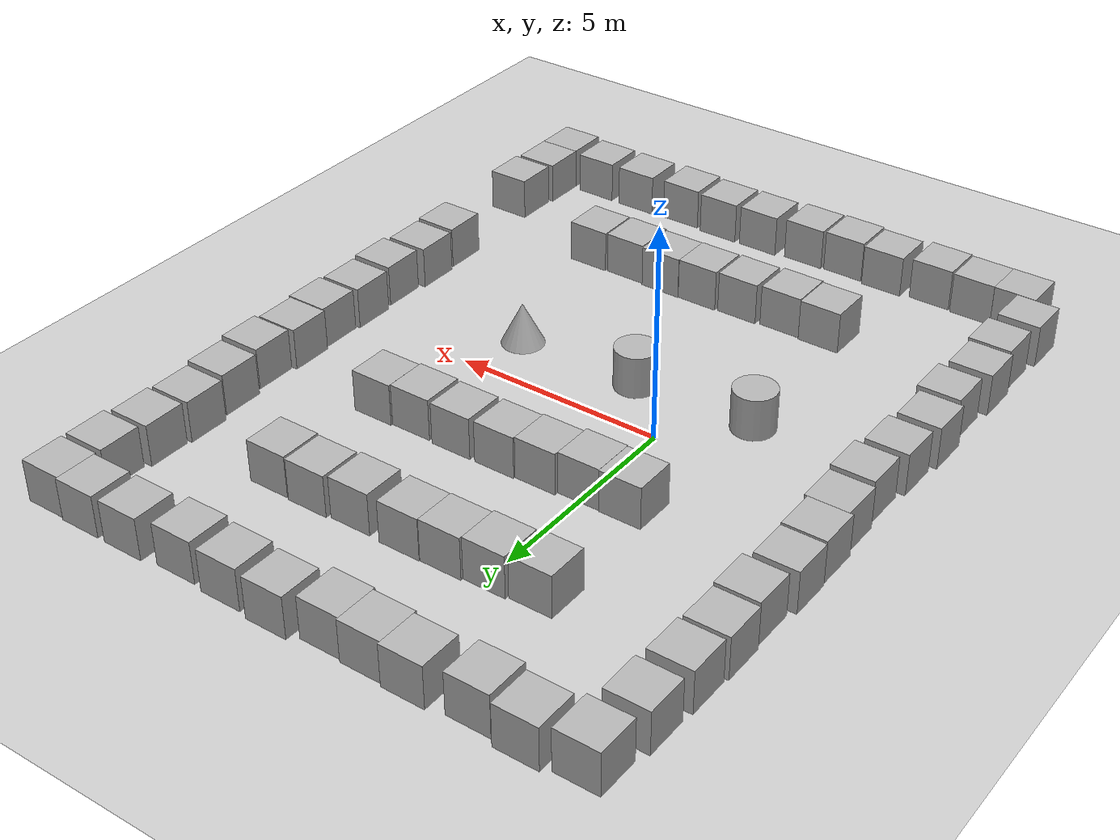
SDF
<?xml version="1.0" ?>
<!-- SEEZY Robot - Supermarket World Simulation                                          -->
<!-- This SDF file defines the Gazebo simulation environment for the SEEZY robot.        -->
<!-- It initializes the basic physics engine (ODE), lighting, gravity, and ground plane. -->
<!-- Note: Additional static models (shelves, walls, obstacles) can be inserted below.   -->
<sdf version='1.10'>
  <world name='supermarket_world'>
    <physics type='ode'>
      <max_step_size>0.01</max_step_size>
      <real_time_factor>1</real_time_factor>
      <real_time_update_rate>1000</real_time_update_rate>
    </physics>
    <gravity>0 0 -9.8000000000000007</gravity>
    <magnetic_field>5.5644999999999998e-06 2.2875799999999999e-05 -4.2388400000000002e-05</magnetic_field>
    <atmosphere type='adiabatic'/>
    <scene>
      <ambient>0.400000006 0.400000006 0.400000006 1</ambient>
      <background>0.699999988 0.699999988 0.699999988 1</background>
      <shadows>true</shadows>
    </scene>
    <model name='ground_plane'>
      <static>true</static>
      <link name='link'>
        <collision name='collision'>
          <geometry>
            <plane>
              <normal>0 0 1</normal>
              <size>1 1</size>
            </plane>
          </geometry>
          <surface>
            <friction>
              <ode/>
            </friction>
            <bounce/>
            <contact/>
          </surface>
        </collision>
        <visual name='visual'>
          <geometry>
            <plane>
              <normal>0 0 1</normal>
              <size>100 100</size>
            </plane>
          </geometry>
          <material>
            <ambient>0.800000012 0.800000012 0.800000012 1</ambient>
            <diffuse>0.800000012 0.800000012 0.800000012 1</diffuse>
            <specular>0.800000012 0.800000012 0.800000012 1</specular>
          </material>
        </visual>
        <pose>0 0 0 0 0 0</pose>
        <inertial>
          <pose>0 0 0 0 0 0</pose>
          <mass>1</mass>
          <inertia>
            <ixx>1</ixx>
            <ixy>0</ixy>
            <ixz>0</ixz>
            <iyy>1</iyy>
            <iyz>0</iyz>
            <izz>1</izz>
          </inertia>
        </inertial>
        <enable_wind>false</enable_wind>
      </link>
      <pose>0 0 0 0 0 0</pose>
      <self_collide>false</self_collide>
    </model>
    <model name='box'>
      <pose>8.3739142428703222 8.4991246552368658 0.49999901997068608 2.2348819397861344e-13 2.2642919251834416e-13 -1.3965656928421165e-06</pose>
      <link name='box_link'>
        <inertial>
          <inertia>
            <ixx>0.16666</ixx>
            <ixy>0</ixy>
            <ixz>0</ixz>
            <iyy>0.16666</iyy>
            <iyz>0</iyz>
            <izz>0.16666</izz>
          </inertia>
          <mass>1</mass>
          <pose>0 0 0 0 0 0</pose>
        </inertial>
        <collision name='box_collision'>
          <geometry>
            <box>
              <size>1 1 1</size>
            </box>
          </geometry>
          <surface>
            <friction>
              <ode/>
            </friction>
            <bounce/>
            <contact/>
          </surface>
        </collision>
        <visual name='box_visual'>
          <geometry>
            <box>
              <size>1 1 1</size>
            </box>
          </geometry>
          <material>
            <ambient>0.300000012 0.300000012 0.300000012 1</ambient>
            <diffuse>0.699999988 0.699999988 0.699999988 1</diffuse>
            <specular>1 1 1 1</specular>
          </material>
        </visual>
        <pose>0 0 0 0 0 0</pose>
        <enable_wind>false</enable_wind>
      </link>
      <static>false</static>
      <self_collide>false</self_collide>
    </model>
    <model name='box_0'>
      <pose>8.3599489400429228 7.3887467499537305 0.49999901997068519 -2.3853049526644058e-19 -5.4921349994193821e-17 -1.5029943223181512e-16</pose>
      <link name='box_link'>
        <inertial>
          <inertia>
            <ixx>0.16666</ixx>
            <ixy>0</ixy>
            <ixz>0</ixz>
            <iyy>0.16666</iyy>
            <iyz>0</iyz>
            <izz>0.16666</izz>
          </inertia>
          <mass>1</mass>
          <pose>0 0 0 0 0 0</pose>
        </inertial>
        <collision name='box_collision'>
          <geometry>
            <box>
              <size>1 1 1</size>
            </box>
          </geometry>
          <surface>
            <friction>
              <ode/>
            </friction>
            <bounce/>
            <contact/>
          </surface>
        </collision>
        <visual name='box_visual'>
          <geometry>
            <box>
              <size>1 1 1</size>
            </box>
          </geometry>
          <material>
            <ambient>0.300000012 0.300000012 0.300000012 1</ambient>
            <diffuse>0.699999988 0.699999988 0.699999988 1</diffuse>
            <specular>1 1 1 1</specular>
          </material>
        </visual>
        <pose>0 0 0 0 0 0</pose>
        <enable_wind>false</enable_wind>
      </link>
      <static>false</static>
      <self_collide>false</self_collide>
    </model>
    <model name='box_1'>
      <pose>8.2394322617933682 6.2924777224729969 0.49999901997068691 7.6335864461754263e-19 -5.4851528614217029e-17 -1.4981461280564556e-16</pose>
      <link name='box_link'>
        <inertial>
          <inertia>
            <ixx>0.16666</ixx>
            <ixy>0</ixy>
            <ixz>0</ixz>
            <iyy>0.16666</iyy>
            <iyz>0</iyz>
            <izz>0.16666</izz>
          </inertia>
          <mass>1</mass>
          <pose>0 0 0 0 0 0</pose>
        </inertial>
        <collision name='box_collision'>
          <geometry>
            <box>
              <size>1 1 1</size>
            </box>
          </geometry>
          <surface>
            <friction>
              <ode/>
            </friction>
            <bounce/>
            <contact/>
          </surface>
        </collision>
        <visual name='box_visual'>
          <geometry>
            <box>
              <size>1 1 1</size>
            </box>
          </geometry>
          <material>
            <ambient>0.300000012 0.300000012 0.300000012 1</ambient>
            <diffuse>0.699999988 0.699999988 0.699999988 1</diffuse>
            <specular>1 1 1 1</specular>
          </material>
        </visual>
        <pose>0 0 0 0 0 0</pose>
        <enable_wind>false</enable_wind>
      </link>
      <static>false</static>
      <self_collide>false</self_collide>
    </model>
    <model name='box_2'>
      <pose>8.178507588848813 5.2159218762847974 0.49999901997068685 -4.6991919186985309e-20 -5.5249783236223348e-17 -1.485242425929306e-16</pose>
      <link name='box_link'>
        <inertial>
          <inertia>
            <ixx>0.16666</ixx>
            <ixy>0</ixy>
            <ixz>0</ixz>
            <iyy>0.16666</iyy>
            <iyz>0</iyz>
            <izz>0.16666</izz>
          </inertia>
          <mass>1</mass>
          <pose>0 0 0 0 0 0</pose>
        </inertial>
        <collision name='box_collision'>
          <geometry>
            <box>
              <size>1 1 1</size>
            </box>
          </geometry>
          <surface>
            <friction>
              <ode/>
            </friction>
            <bounce/>
            <contact/>
          </surface>
        </collision>
        <visual name='box_visual'>
          <geometry>
            <box>
              <size>1 1 1</size>
            </box>
          </geometry>
          <material>
            <ambient>0.300000012 0.300000012 0.300000012 1</ambient>
            <diffuse>0.699999988 0.699999988 0.699999988 1</diffuse>
            <specular>1 1 1 1</specular>
          </material>
        </visual>
        <pose>0 0 0 0 0 0</pose>
        <enable_wind>false</enable_wind>
      </link>
      <static>false</static>
      <self_collide>false</self_collide>
    </model>
    <model name='box_3'>
      <pose>8.292137907557251 4.0878692709566833 0.49999901997068602 9.9941326737012215e-19 -5.3861476501093767e-17 1.051353151830816e-16</pose>
      <link name='box_link'>
        <inertial>
          <inertia>
            <ixx>0.16666</ixx>
            <ixy>0</ixy>
            <ixz>0</ixz>
            <iyy>0.16666</iyy>
            <iyz>0</iyz>
            <izz>0.16666</izz>
          </inertia>
          <mass>1</mass>
          <pose>0 0 0 0 0 0</pose>
        </inertial>
        <collision name='box_collision'>
          <geometry>
            <box>
              <size>1 1 1</size>
            </box>
          </geometry>
          <surface>
            <friction>
              <ode/>
            </friction>
            <bounce/>
            <contact/>
          </surface>
        </collision>
        <visual name='box_visual'>
          <geometry>
            <box>
              <size>1 1 1</size>
            </box>
          </geometry>
          <material>
            <ambient>0.300000012 0.300000012 0.300000012 1</ambient>
            <diffuse>0.699999988 0.699999988 0.699999988 1</diffuse>
            <specular>1 1 1 1</specular>
          </material>
        </visual>
        <pose>0 0 0 0 0 0</pose>
        <enable_wind>false</enable_wind>
      </link>
      <static>false</static>
      <self_collide>false</self_collide>
    </model>
    <model name='box_4'>
      <pose>8.4065443264111295 2.9521080647178528 0.49999901997068702 -1.9355377213800176e-19 -5.5068632770077421e-17 -1.4843682263452473e-16</pose>
      <link name='box_link'>
        <inertial>
          <inertia>
            <ixx>0.16666</ixx>
            <ixy>0</ixy>
            <ixz>0</ixz>
            <iyy>0.16666</iyy>
            <iyz>0</iyz>
            <izz>0.16666</izz>
          </inertia>
          <mass>1</mass>
          <pose>0 0 0 0 0 0</pose>
        </inertial>
        <collision name='box_collision'>
          <geometry>
            <box>
              <size>1 1 1</size>
            </box>
          </geometry>
          <surface>
            <friction>
              <ode/>
            </friction>
            <bounce/>
            <contact/>
          </surface>
        </collision>
        <visual name='box_visual'>
          <geometry>
            <box>
              <size>1 1 1</size>
            </box>
          </geometry>
          <material>
            <ambient>0.300000012 0.300000012 0.300000012 1</ambient>
            <diffuse>0.699999988 0.699999988 0.699999988 1</diffuse>
            <specular>1 1 1 1</specular>
          </material>
        </visual>
        <pose>0 0 0 0 0 0</pose>
        <enable_wind>false</enable_wind>
      </link>
      <static>false</static>
      <self_collide>false</self_collide>
    </model>
    <model name='box_5'>
      <pose>8.2921371315712555 1.911037588665371 0.49999901997068602 5.4462563294215104e-17 1.2736077551306983e-19 -1.3626328609519604e-17</pose>
      <link name='box_link'>
        <inertial>
          <inertia>
            <ixx>0.16666</ixx>
            <ixy>0</ixy>
            <ixz>0</ixz>
            <iyy>0.16666</iyy>
            <iyz>0</iyz>
            <izz>0.16666</izz>
          </inertia>
          <mass>1</mass>
          <pose>0 0 0 0 0 0</pose>
        </inertial>
        <collision name='box_collision'>
          <geometry>
            <box>
              <size>1 1 1</size>
            </box>
          </geometry>
          <surface>
            <friction>
              <ode/>
            </friction>
            <bounce/>
            <contact/>
          </surface>
        </collision>
        <visual name='box_visual'>
          <geometry>
            <box>
              <size>1 1 1</size>
            </box>
          </geometry>
          <material>
            <ambient>0.300000012 0.300000012 0.300000012 1</ambient>
            <diffuse>0.699999988 0.699999988 0.699999988 1</diffuse>
            <specular>1 1 1 1</specular>
          </material>
        </visual>
        <pose>0 0 0 0 0 0</pose>
        <enable_wind>false</enable_wind>
      </link>
      <static>false</static>
      <self_collide>false</self_collide>
    </model>
    <model name='box_6'>
      <pose>8.3599477570648091 0.88502298679097557 0.4999990199706873 -5.4766448174674108e-17 -7.8348344244661134e-20 -3.3200572492622903e-17</pose>
      <link name='box_link'>
        <inertial>
          <inertia>
            <ixx>0.16666</ixx>
            <ixy>0</ixy>
            <ixz>0</ixz>
            <iyy>0.16666</iyy>
            <iyz>0</iyz>
            <izz>0.16666</izz>
          </inertia>
          <mass>1</mass>
          <pose>0 0 0 0 0 0</pose>
        </inertial>
        <collision name='box_collision'>
          <geometry>
            <box>
              <size>1 1 1</size>
            </box>
          </geometry>
          <surface>
            <friction>
              <ode/>
            </friction>
            <bounce/>
            <contact/>
          </surface>
        </collision>
        <visual name='box_visual'>
          <geometry>
            <box>
              <size>1 1 1</size>
            </box>
          </geometry>
          <material>
            <ambient>0.300000012 0.300000012 0.300000012 1</ambient>
            <diffuse>0.699999988 0.699999988 0.699999988 1</diffuse>
            <specular>1 1 1 1</specular>
          </material>
        </visual>
        <pose>0 0 0 0 0 0</pose>
        <enable_wind>false</enable_wind>
      </link>
      <static>false</static>
      <self_collide>false</self_collide>
    </model>
    <model name='box_7'>
      <pose>8.2921380726471874 -0.18658887087335663 0.49999901997068646 5.4312585427724196e-17 -7.3745845500765171e-19 -1.1733470305338631e-16</pose>
      <link name='box_link'>
        <inertial>
          <inertia>
            <ixx>0.16666</ixx>
            <ixy>0</ixy>
            <ixz>0</ixz>
            <iyy>0.16666</iyy>
            <iyz>0</iyz>
            <izz>0.16666</izz>
          </inertia>
          <mass>1</mass>
          <pose>0 0 0 0 0 0</pose>
        </inertial>
        <collision name='box_collision'>
          <geometry>
            <box>
              <size>1 1 1</size>
            </box>
          </geometry>
          <surface>
            <friction>
              <ode/>
            </friction>
            <bounce/>
            <contact/>
          </surface>
        </collision>
        <visual name='box_visual'>
          <geometry>
            <box>
              <size>1 1 1</size>
            </box>
          </geometry>
          <material>
            <ambient>0.300000012 0.300000012 0.300000012 1</ambient>
            <diffuse>0.699999988 0.699999988 0.699999988 1</diffuse>
            <specular>1 1 1 1</specular>
          </material>
        </visual>
        <pose>0 0 0 0 0 0</pose>
        <enable_wind>false</enable_wind>
      </link>
      <static>false</static>
      <self_collide>false</self_collide>
    </model>
    <model name='box_8'>
      <pose>8.35994921766601 -1.3357347856292385 0.49999901997068585 -3.5316034493105225e-19 -5.4564616593038525e-17 -1.4888627611804775e-16</pose>
      <link name='box_link'>
        <inertial>
          <inertia>
            <ixx>0.16666</ixx>
            <ixy>0</ixy>
            <ixz>0</ixz>
            <iyy>0.16666</iyy>
            <iyz>0</iyz>
            <izz>0.16666</izz>
          </inertia>
          <mass>1</mass>
          <pose>0 0 0 0 0 0</pose>
        </inertial>
        <collision name='box_collision'>
          <geometry>
            <box>
              <size>1 1 1</size>
            </box>
          </geometry>
          <surface>
            <friction>
              <ode/>
            </friction>
            <bounce/>
            <contact/>
          </surface>
        </collision>
        <visual name='box_visual'>
          <geometry>
            <box>
              <size>1 1 1</size>
            </box>
          </geometry>
          <material>
            <ambient>0.300000012 0.300000012 0.300000012 1</ambient>
            <diffuse>0.699999988 0.699999988 0.699999988 1</diffuse>
            <specular>1 1 1 1</specular>
          </material>
        </visual>
        <pose>0 0 0 0 0 0</pose>
        <enable_wind>false</enable_wind>
      </link>
      <static>false</static>
      <self_collide>false</self_collide>
    </model>
    <model name='box_9'>
      <pose>8.2394319175730963 -2.4393221170170669 0.49999901997068535 -1.2747921174698496e-19 -5.5453399765897063e-17 -1.5229980923750203e-16</pose>
      <link name='box_link'>
        <inertial>
          <inertia>
            <ixx>0.16666</ixx>
            <ixy>0</ixy>
            <ixz>0</ixz>
            <iyy>0.16666</iyy>
            <iyz>0</iyz>
            <izz>0.16666</izz>
          </inertia>
          <mass>1</mass>
          <pose>0 0 0 0 0 0</pose>
        </inertial>
        <collision name='box_collision'>
          <geometry>
            <box>
              <size>1 1 1</size>
            </box>
          </geometry>
          <surface>
            <friction>
              <ode/>
            </friction>
            <bounce/>
            <contact/>
          </surface>
        </collision>
        <visual name='box_visual'>
          <geometry>
            <box>
              <size>1 1 1</size>
            </box>
          </geometry>
          <material>
            <ambient>0.300000012 0.300000012 0.300000012 1</ambient>
            <diffuse>0.699999988 0.699999988 0.699999988 1</diffuse>
            <specular>1 1 1 1</specular>
          </material>
        </visual>
        <pose>0 0 0 0 0 0</pose>
        <enable_wind>false</enable_wind>
      </link>
      <static>false</static>
      <self_collide>false</self_collide>
    </model>
    <model name='box_10'>
      <pose>8.292137985640025 -3.5504486111469227 0.49999901997068585 2.5119105073607024e-19 -5.4565259392399407e-17 2.6240833761110909e-17</pose>
      <link name='box_link'>
        <inertial>
          <inertia>
            <ixx>0.16666</ixx>
            <ixy>0</ixy>
            <ixz>0</ixz>
            <iyy>0.16666</iyy>
            <iyz>0</iyz>
            <izz>0.16666</izz>
          </inertia>
          <mass>1</mass>
          <pose>0 0 0 0 0 0</pose>
        </inertial>
        <collision name='box_collision'>
          <geometry>
            <box>
              <size>1 1 1</size>
            </box>
          </geometry>
          <surface>
            <friction>
              <ode/>
            </friction>
            <bounce/>
            <contact/>
          </surface>
        </collision>
        <visual name='box_visual'>
          <geometry>
            <box>
              <size>1 1 1</size>
            </box>
          </geometry>
          <material>
            <ambient>0.300000012 0.300000012 0.300000012 1</ambient>
            <diffuse>0.699999988 0.699999988 0.699999988 1</diffuse>
            <specular>1 1 1 1</specular>
          </material>
        </visual>
        <pose>0 0 0 0 0 0</pose>
        <enable_wind>false</enable_wind>
      </link>
      <static>false</static>
      <self_collide>false</self_collide>
    </model>
    <model name='box_11'>
      <pose>8.3599484130359762 -6.4911661344040112 0.49999901997068685 1.2184321968921324e-19 -5.4896099746309551e-17 -1.4904533393108512e-16</pose>
      <link name='box_link'>
        <inertial>
          <inertia>
            <ixx>0.16666</ixx>
            <ixy>0</ixy>
            <ixz>0</ixz>
            <iyy>0.16666</iyy>
            <iyz>0</iyz>
            <izz>0.16666</izz>
          </inertia>
          <mass>1</mass>
          <pose>0 0 0 0 0 0</pose>
        </inertial>
        <collision name='box_collision'>
          <geometry>
            <box>
              <size>1 1 1</size>
            </box>
          </geometry>
          <surface>
            <friction>
              <ode/>
            </friction>
            <bounce/>
            <contact/>
          </surface>
        </collision>
        <visual name='box_visual'>
          <geometry>
            <box>
              <size>1 1 1</size>
            </box>
          </geometry>
          <material>
            <ambient>0.300000012 0.300000012 0.300000012 1</ambient>
            <diffuse>0.699999988 0.699999988 0.699999988 1</diffuse>
            <specular>1 1 1 1</specular>
          </material>
        </visual>
        <pose>0 0 0 0 0 0</pose>
        <enable_wind>false</enable_wind>
      </link>
      <static>false</static>
      <self_collide>false</self_collide>
    </model>
    <model name='box_12'>
      <pose>8.292138975080519 -7.5816466128785995 0.4999990199706868 -2.2698675383332317e-13 -2.2643068329978488e-13 1.644982497892697e-06</pose>
      <link name='box_link'>
        <inertial>
          <inertia>
            <ixx>0.16666</ixx>
            <ixy>0</ixy>
            <ixz>0</ixz>
            <iyy>0.16666</iyy>
            <iyz>0</iyz>
            <izz>0.16666</izz>
          </inertia>
          <mass>1</mass>
          <pose>0 0 0 0 0 0</pose>
        </inertial>
        <collision name='box_collision'>
          <geometry>
            <box>
              <size>1 1 1</size>
            </box>
          </geometry>
          <surface>
            <friction>
              <ode/>
            </friction>
            <bounce/>
            <contact/>
          </surface>
        </collision>
        <visual name='box_visual'>
          <geometry>
            <box>
              <size>1 1 1</size>
            </box>
          </geometry>
          <material>
            <ambient>0.300000012 0.300000012 0.300000012 1</ambient>
            <diffuse>0.699999988 0.699999988 0.699999988 1</diffuse>
            <specular>1 1 1 1</specular>
          </material>
        </visual>
        <pose>0 0 0 0 0 0</pose>
        <enable_wind>false</enable_wind>
      </link>
      <static>false</static>
      <self_collide>false</self_collide>
    </model>
    <model name='box_13'>
      <pose>8.292137527113967 -8.5816466128823734 0.49999901997068597 2.2076708296356033e-13 -2.2431498138324399e-13 1.6449824978575932e-06</pose>
      <link name='box_link'>
        <inertial>
          <inertia>
            <ixx>0.16666</ixx>
            <ixy>0</ixy>
            <ixz>0</ixz>
            <iyy>0.16666</iyy>
            <iyz>0</iyz>
            <izz>0.16666</izz>
          </inertia>
          <mass>1</mass>
          <pose>0 0 0 0 0 0</pose>
        </inertial>
        <collision name='box_collision'>
          <geometry>
            <box>
              <size>1 1 1</size>
            </box>
          </geometry>
          <surface>
            <friction>
              <ode/>
            </friction>
            <bounce/>
            <contact/>
          </surface>
        </collision>
        <visual name='box_visual'>
          <geometry>
            <box>
              <size>1 1 1</size>
            </box>
          </geometry>
          <material>
            <ambient>0.300000012 0.300000012 0.300000012 1</ambient>
            <diffuse>0.699999988 0.699999988 0.699999988 1</diffuse>
            <specular>1 1 1 1</specular>
          </material>
        </visual>
        <pose>0 0 0 0 0 0</pose>
        <enable_wind>false</enable_wind>
      </link>
      <static>false</static>
      <self_collide>false</self_collide>
    </model>
    <model name='box_14'>
      <pose>7.1004684341563049 -8.4840748178244016 0.49999901997068641 1.4005283284370249e-19 -5.5581335430422208e-17 -1.7015719702994222e-16</pose>
      <link name='box_link'>
        <inertial>
          <inertia>
            <ixx>0.16666</ixx>
            <ixy>0</ixy>
            <ixz>0</ixz>
            <iyy>0.16666</iyy>
            <iyz>0</iyz>
            <izz>0.16666</izz>
          </inertia>
          <mass>1</mass>
          <pose>0 0 0 0 0 0</pose>
        </inertial>
        <collision name='box_collision'>
          <geometry>
            <box>
              <size>1 1 1</size>
            </box>
          </geometry>
          <surface>
            <friction>
              <ode/>
            </friction>
            <bounce/>
            <contact/>
          </surface>
        </collision>
        <visual name='box_visual'>
          <geometry>
            <box>
              <size>1 1 1</size>
            </box>
          </geometry>
          <material>
            <ambient>0.300000012 0.300000012 0.300000012 1</ambient>
            <diffuse>0.699999988 0.699999988 0.699999988 1</diffuse>
            <specular>1 1 1 1</specular>
          </material>
        </visual>
        <pose>0 0 0 0 0 0</pose>
        <enable_wind>false</enable_wind>
      </link>
      <static>false</static>
      <self_collide>false</self_collide>
    </model>
    <model name='box_15'>
      <pose>5.8868902017453415 -8.483177013111673 0.49999901997068541 5.0667621786247898e-19 -5.4722843813639268e-17 -2.007705083077993e-16</pose>
      <link name='box_link'>
        <inertial>
          <inertia>
            <ixx>0.16666</ixx>
            <ixy>0</ixy>
            <ixz>0</ixz>
            <iyy>0.16666</iyy>
            <iyz>0</iyz>
            <izz>0.16666</izz>
          </inertia>
          <mass>1</mass>
          <pose>0 0 0 0 0 0</pose>
        </inertial>
        <collision name='box_collision'>
          <geometry>
            <box>
              <size>1 1 1</size>
            </box>
          </geometry>
          <surface>
            <friction>
              <ode/>
            </friction>
            <bounce/>
            <contact/>
          </surface>
        </collision>
        <visual name='box_visual'>
          <geometry>
            <box>
              <size>1 1 1</size>
            </box>
          </geometry>
          <material>
            <ambient>0.300000012 0.300000012 0.300000012 1</ambient>
            <diffuse>0.699999988 0.699999988 0.699999988 1</diffuse>
            <specular>1 1 1 1</specular>
          </material>
        </visual>
        <pose>0 0 0 0 0 0</pose>
        <enable_wind>false</enable_wind>
      </link>
      <static>false</static>
      <self_collide>false</self_collide>
    </model>
    <model name='box_16'>
      <pose>4.5793990559907982 -8.5402041557433961 0.49999901997068702 3.4103993743557963e-19 -5.4650942151699583e-17 -1.7995828096061792e-16</pose>
      <link name='box_link'>
        <inertial>
          <inertia>
            <ixx>0.16666</ixx>
            <ixy>0</ixy>
            <ixz>0</ixz>
            <iyy>0.16666</iyy>
            <iyz>0</iyz>
            <izz>0.16666</izz>
          </inertia>
          <mass>1</mass>
          <pose>0 0 0 0 0 0</pose>
        </inertial>
        <collision name='box_collision'>
          <geometry>
            <box>
              <size>1 1 1</size>
            </box>
          </geometry>
          <surface>
            <friction>
              <ode/>
            </friction>
            <bounce/>
            <contact/>
          </surface>
        </collision>
        <visual name='box_visual'>
          <geometry>
            <box>
              <size>1 1 1</size>
            </box>
          </geometry>
          <material>
            <ambient>0.300000012 0.300000012 0.300000012 1</ambient>
            <diffuse>0.699999988 0.699999988 0.699999988 1</diffuse>
            <specular>1 1 1 1</specular>
          </material>
        </visual>
        <pose>0 0 0 0 0 0</pose>
        <enable_wind>false</enable_wind>
      </link>
      <static>false</static>
      <self_collide>false</self_collide>
    </model>
    <model name='box_17'>
      <pose>3.4560056745353656 -8.4785526730327092 0.49999901997068719 2.9975159588562845e-19 -5.5282934451014012e-17 -1.4885680688878971e-16</pose>
      <link name='box_link'>
        <inertial>
          <inertia>
            <ixx>0.16666</ixx>
            <ixy>0</ixy>
            <ixz>0</ixz>
            <iyy>0.16666</iyy>
            <iyz>0</iyz>
            <izz>0.16666</izz>
          </inertia>
          <mass>1</mass>
          <pose>0 0 0 0 0 0</pose>
        </inertial>
        <collision name='box_collision'>
          <geometry>
            <box>
              <size>1 1 1</size>
            </box>
          </geometry>
          <surface>
            <friction>
              <ode/>
            </friction>
            <bounce/>
            <contact/>
          </surface>
        </collision>
        <visual name='box_visual'>
          <geometry>
            <box>
              <size>1 1 1</size>
            </box>
          </geometry>
          <material>
            <ambient>0.300000012 0.300000012 0.300000012 1</ambient>
            <diffuse>0.699999988 0.699999988 0.699999988 1</diffuse>
            <specular>1 1 1 1</specular>
          </material>
        </visual>
        <pose>0 0 0 0 0 0</pose>
        <enable_wind>false</enable_wind>
      </link>
      <static>false</static>
      <self_collide>false</self_collide>
    </model>
    <model name='box_18'>
      <pose>2.3368050941580982 -8.4969861346112285 0.49999901997068563 8.9921862608866556e-19 -5.4810453830300779e-17 -1.4942994026736365e-16</pose>
      <link name='box_link'>
        <inertial>
          <inertia>
            <ixx>0.16666</ixx>
            <ixy>0</ixy>
            <ixz>0</ixz>
            <iyy>0.16666</iyy>
            <iyz>0</iyz>
            <izz>0.16666</izz>
          </inertia>
          <mass>1</mass>
          <pose>0 0 0 0 0 0</pose>
        </inertial>
        <collision name='box_collision'>
          <geometry>
            <box>
              <size>1 1 1</size>
            </box>
          </geometry>
          <surface>
            <friction>
              <ode/>
            </friction>
            <bounce/>
            <contact/>
          </surface>
        </collision>
        <visual name='box_visual'>
          <geometry>
            <box>
              <size>1 1 1</size>
            </box>
          </geometry>
          <material>
            <ambient>0.300000012 0.300000012 0.300000012 1</ambient>
            <diffuse>0.699999988 0.699999988 0.699999988 1</diffuse>
            <specular>1 1 1 1</specular>
          </material>
        </visual>
        <pose>0 0 0 0 0 0</pose>
        <enable_wind>false</enable_wind>
      </link>
      <static>false</static>
      <self_collide>false</self_collide>
    </model>
    <model name='box_19'>
      <pose>1.1209091555754185 -8.5856432976933625 0.49999901997068574 2.8614643890754435e-19 -5.5290314063770497e-17 -1.5071632751643689e-16</pose>
      <link name='box_link'>
        <inertial>
          <inertia>
            <ixx>0.16666</ixx>
            <ixy>0</ixy>
            <ixz>0</ixz>
            <iyy>0.16666</iyy>
            <iyz>0</iyz>
            <izz>0.16666</izz>
          </inertia>
          <mass>1</mass>
          <pose>0 0 0 0 0 0</pose>
        </inertial>
        <collision name='box_collision'>
          <geometry>
            <box>
              <size>1 1 1</size>
            </box>
          </geometry>
          <surface>
            <friction>
              <ode/>
            </friction>
            <bounce/>
            <contact/>
          </surface>
        </collision>
        <visual name='box_visual'>
          <geometry>
            <box>
              <size>1 1 1</size>
            </box>
          </geometry>
          <material>
            <ambient>0.300000012 0.300000012 0.300000012 1</ambient>
            <diffuse>0.699999988 0.699999988 0.699999988 1</diffuse>
            <specular>1 1 1 1</specular>
          </material>
        </visual>
        <pose>0 0 0 0 0 0</pose>
        <enable_wind>false</enable_wind>
      </link>
      <static>false</static>
      <self_collide>false</self_collide>
    </model>
    <model name='box_20'>
      <pose>0.063885025016571007 -8.6244510410214197 0.49999901997068608 3.8644102242571229e-17 1.718197545714921e-17 -7.6517660015406847e-17</pose>
      <link name='box_link'>
        <inertial>
          <inertia>
            <ixx>0.16666</ixx>
            <ixy>0</ixy>
            <ixz>0</ixz>
            <iyy>0.16666</iyy>
            <iyz>0</iyz>
            <izz>0.16666</izz>
          </inertia>
          <mass>1</mass>
          <pose>0 0 0 0 0 0</pose>
        </inertial>
        <collision name='box_collision'>
          <geometry>
            <box>
              <size>1 1 1</size>
            </box>
          </geometry>
          <surface>
            <friction>
              <ode/>
            </friction>
            <bounce/>
            <contact/>
          </surface>
        </collision>
        <visual name='box_visual'>
          <geometry>
            <box>
              <size>1 1 1</size>
            </box>
          </geometry>
          <material>
            <ambient>0.300000012 0.300000012 0.300000012 1</ambient>
            <diffuse>0.699999988 0.699999988 0.699999988 1</diffuse>
            <specular>1 1 1 1</specular>
          </material>
        </visual>
        <pose>0 0 0 0 0 0</pose>
        <enable_wind>false</enable_wind>
      </link>
      <static>false</static>
      <self_collide>false</self_collide>
    </model>
    <model name='box_21'>
      <pose>-0.99485717680037133 -8.5476532571397055 0.49999901997068674 5.5218092506242785e-17 1.3141559468966683e-19 -5.8559794383059209e-17</pose>
      <link name='box_link'>
        <inertial>
          <inertia>
            <ixx>0.16666</ixx>
            <ixy>0</ixy>
            <ixz>0</ixz>
            <iyy>0.16666</iyy>
            <iyz>0</iyz>
            <izz>0.16666</izz>
          </inertia>
          <mass>1</mass>
          <pose>0 0 0 0 0 0</pose>
        </inertial>
        <collision name='box_collision'>
          <geometry>
            <box>
              <size>1 1 1</size>
            </box>
          </geometry>
          <surface>
            <friction>
              <ode/>
            </friction>
            <bounce/>
            <contact/>
          </surface>
        </collision>
        <visual name='box_visual'>
          <geometry>
            <box>
              <size>1 1 1</size>
            </box>
          </geometry>
          <material>
            <ambient>0.300000012 0.300000012 0.300000012 1</ambient>
            <diffuse>0.699999988 0.699999988 0.699999988 1</diffuse>
            <specular>1 1 1 1</specular>
          </material>
        </visual>
        <pose>0 0 0 0 0 0</pose>
        <enable_wind>false</enable_wind>
      </link>
      <static>false</static>
      <self_collide>false</self_collide>
    </model>
    <model name='box_22'>
      <pose>7.3739143010869102 8.5408454410218173 0.49999901997068646 -2.2687344525636568e-13 -2.2659581979661127e-13 -1.3966704911623266e-06</pose>
      <link name='box_link'>
        <inertial>
          <inertia>
            <ixx>0.16666</ixx>
            <ixy>0</ixy>
            <ixz>0</ixz>
            <iyy>0.16666</iyy>
            <iyz>0</iyz>
            <izz>0.16666</izz>
          </inertia>
          <mass>1</mass>
          <pose>0 0 0 0 0 0</pose>
        </inertial>
        <collision name='box_collision'>
          <geometry>
            <box>
              <size>1 1 1</size>
            </box>
          </geometry>
          <surface>
            <friction>
              <ode/>
            </friction>
            <bounce/>
            <contact/>
          </surface>
        </collision>
        <visual name='box_visual'>
          <geometry>
            <box>
              <size>1 1 1</size>
            </box>
          </geometry>
          <material>
            <ambient>0.300000012 0.300000012 0.300000012 1</ambient>
            <diffuse>0.699999988 0.699999988 0.699999988 1</diffuse>
            <specular>1 1 1 1</specular>
          </material>
        </visual>
        <pose>0 0 0 0 0 0</pose>
        <enable_wind>false</enable_wind>
      </link>
      <static>false</static>
      <self_collide>false</self_collide>
    </model>
    <model name='box_23'>
      <pose>6.1925632018410752 8.5437907844867294 0.49999901997068674 -3.2626995193616972e-19 -5.5331886286950457e-17 -1.481976748723888e-16</pose>
      <link name='box_link'>
        <inertial>
          <inertia>
            <ixx>0.16666</ixx>
            <ixy>0</ixy>
            <ixz>0</ixz>
            <iyy>0.16666</iyy>
            <iyz>0</iyz>
            <izz>0.16666</izz>
          </inertia>
          <mass>1</mass>
          <pose>0 0 0 0 0 0</pose>
        </inertial>
        <collision name='box_collision'>
          <geometry>
            <box>
              <size>1 1 1</size>
            </box>
          </geometry>
          <surface>
            <friction>
              <ode/>
            </friction>
            <bounce/>
            <contact/>
          </surface>
        </collision>
        <visual name='box_visual'>
          <geometry>
            <box>
              <size>1 1 1</size>
            </box>
          </geometry>
          <material>
            <ambient>0.300000012 0.300000012 0.300000012 1</ambient>
            <diffuse>0.699999988 0.699999988 0.699999988 1</diffuse>
            <specular>1 1 1 1</specular>
          </material>
        </visual>
        <pose>0 0 0 0 0 0</pose>
        <enable_wind>false</enable_wind>
      </link>
      <static>false</static>
      <self_collide>false</self_collide>
    </model>
    <model name='box_24'>
      <pose>4.8598208546270243 8.4412858325604621 0.49999901997068563 8.3329809958881114e-19 -5.4611164746740497e-17 -1.7681699454392143e-16</pose>
      <link name='box_link'>
        <inertial>
          <inertia>
            <ixx>0.16666</ixx>
            <ixy>0</ixy>
            <ixz>0</ixz>
            <iyy>0.16666</iyy>
            <iyz>0</iyz>
            <izz>0.16666</izz>
          </inertia>
          <mass>1</mass>
          <pose>0 0 0 0 0 0</pose>
        </inertial>
        <collision name='box_collision'>
          <geometry>
            <box>
              <size>1 1 1</size>
            </box>
          </geometry>
          <surface>
            <friction>
              <ode/>
            </friction>
            <bounce/>
            <contact/>
          </surface>
        </collision>
        <visual name='box_visual'>
          <geometry>
            <box>
              <size>1 1 1</size>
            </box>
          </geometry>
          <material>
            <ambient>0.300000012 0.300000012 0.300000012 1</ambient>
            <diffuse>0.699999988 0.699999988 0.699999988 1</diffuse>
            <specular>1 1 1 1</specular>
          </material>
        </visual>
        <pose>0 0 0 0 0 0</pose>
        <enable_wind>false</enable_wind>
      </link>
      <static>false</static>
      <self_collide>false</self_collide>
    </model>
    <model name='box_25'>
      <pose>3.6288153357328596 8.5131392015221596 0.49999901997068702 7.5795713634588209e-18 4.5318898567860741e-17 -2.557994157569388e-17</pose>
      <link name='box_link'>
        <inertial>
          <inertia>
            <ixx>0.16666</ixx>
            <ixy>0</ixy>
            <ixz>0</ixz>
            <iyy>0.16666</iyy>
            <iyz>0</iyz>
            <izz>0.16666</izz>
          </inertia>
          <mass>1</mass>
          <pose>0 0 0 0 0 0</pose>
        </inertial>
        <collision name='box_collision'>
          <geometry>
            <box>
              <size>1 1 1</size>
            </box>
          </geometry>
          <surface>
            <friction>
              <ode/>
            </friction>
            <bounce/>
            <contact/>
          </surface>
        </collision>
        <visual name='box_visual'>
          <geometry>
            <box>
              <size>1 1 1</size>
            </box>
          </geometry>
          <material>
            <ambient>0.300000012 0.300000012 0.300000012 1</ambient>
            <diffuse>0.699999988 0.699999988 0.699999988 1</diffuse>
            <specular>1 1 1 1</specular>
          </material>
        </visual>
        <pose>0 0 0 0 0 0</pose>
        <enable_wind>false</enable_wind>
      </link>
      <static>false</static>
      <self_collide>false</self_collide>
    </model>
    <model name='box_26'>
      <pose>2.414128419637958 8.5882807453552505 0.49999901997068619 1.882832800260505e-19 -5.4284439081905873e-17 1.0280165663289892e-16</pose>
      <link name='box_link'>
        <inertial>
          <inertia>
            <ixx>0.16666</ixx>
            <ixy>0</ixy>
            <ixz>0</ixz>
            <iyy>0.16666</iyy>
            <iyz>0</iyz>
            <izz>0.16666</izz>
          </inertia>
          <mass>1</mass>
          <pose>0 0 0 0 0 0</pose>
        </inertial>
        <collision name='box_collision'>
          <geometry>
            <box>
              <size>1 1 1</size>
            </box>
          </geometry>
          <surface>
            <friction>
              <ode/>
            </friction>
            <bounce/>
            <contact/>
          </surface>
        </collision>
        <visual name='box_visual'>
          <geometry>
            <box>
              <size>1 1 1</size>
            </box>
          </geometry>
          <material>
            <ambient>0.300000012 0.300000012 0.300000012 1</ambient>
            <diffuse>0.699999988 0.699999988 0.699999988 1</diffuse>
            <specular>1 1 1 1</specular>
          </material>
        </visual>
        <pose>0 0 0 0 0 0</pose>
        <enable_wind>false</enable_wind>
      </link>
      <static>false</static>
      <self_collide>false</self_collide>
    </model>
    <model name='box_27'>
      <pose>1.2348357508965624 8.4158151928005349 0.49999901997068696 2.243737553596623e-13 2.2639404052500012e-13 -2.6295876719116184e-06</pose>
      <link name='box_link'>
        <inertial>
          <inertia>
            <ixx>0.16666</ixx>
            <ixy>0</ixy>
            <ixz>0</ixz>
            <iyy>0.16666</iyy>
            <iyz>0</iyz>
            <izz>0.16666</izz>
          </inertia>
          <mass>1</mass>
          <pose>0 0 0 0 0 0</pose>
        </inertial>
        <collision name='box_collision'>
          <geometry>
            <box>
              <size>1 1 1</size>
            </box>
          </geometry>
          <surface>
            <friction>
              <ode/>
            </friction>
            <bounce/>
            <contact/>
          </surface>
        </collision>
        <visual name='box_visual'>
          <geometry>
            <box>
              <size>1 1 1</size>
            </box>
          </geometry>
          <material>
            <ambient>0.300000012 0.300000012 0.300000012 1</ambient>
            <diffuse>0.699999988 0.699999988 0.699999988 1</diffuse>
            <specular>1 1 1 1</specular>
          </material>
        </visual>
        <pose>0 0 0 0 0 0</pose>
        <enable_wind>false</enable_wind>
      </link>
      <static>false</static>
      <self_collide>false</self_collide>
    </model>
    <model name='box_28'>
      <pose>0.23483588385592666 8.4664159340604375 0.49999901997068619 -2.2379747286635238e-13 -3.5939786468945832e-16 -2.6298016045821032e-06</pose>
      <link name='box_link'>
        <inertial>
          <inertia>
            <ixx>0.16666</ixx>
            <ixy>0</ixy>
            <ixz>0</ixz>
            <iyy>0.16666</iyy>
            <iyz>0</iyz>
            <izz>0.16666</izz>
          </inertia>
          <mass>1</mass>
          <pose>0 0 0 0 0 0</pose>
        </inertial>
        <collision name='box_collision'>
          <geometry>
            <box>
              <size>1 1 1</size>
            </box>
          </geometry>
          <surface>
            <friction>
              <ode/>
            </friction>
            <bounce/>
            <contact/>
          </surface>
        </collision>
        <visual name='box_visual'>
          <geometry>
            <box>
              <size>1 1 1</size>
            </box>
          </geometry>
          <material>
            <ambient>0.300000012 0.300000012 0.300000012 1</ambient>
            <diffuse>0.699999988 0.699999988 0.699999988 1</diffuse>
            <specular>1 1 1 1</specular>
          </material>
        </visual>
        <pose>0 0 0 0 0 0</pose>
        <enable_wind>false</enable_wind>
      </link>
      <static>false</static>
      <self_collide>false</self_collide>
    </model>
    <model name='box_29'>
      <pose>-0.76516396093762096 8.5254571143618723 0.49999901997068585 2.2332113832420632e-13 -2.2126756181625804e-13 -2.6299298669604461e-06</pose>
      <link name='box_link'>
        <inertial>
          <inertia>
            <ixx>0.16666</ixx>
            <ixy>0</ixy>
            <ixz>0</ixz>
            <iyy>0.16666</iyy>
            <iyz>0</iyz>
            <izz>0.16666</izz>
          </inertia>
          <mass>1</mass>
          <pose>0 0 0 0 0 0</pose>
        </inertial>
        <collision name='box_collision'>
          <geometry>
            <box>
              <size>1 1 1</size>
            </box>
          </geometry>
          <surface>
            <friction>
              <ode/>
            </friction>
            <bounce/>
            <contact/>
          </surface>
        </collision>
        <visual name='box_visual'>
          <geometry>
            <box>
              <size>1 1 1</size>
            </box>
          </geometry>
          <material>
            <ambient>0.300000012 0.300000012 0.300000012 1</ambient>
            <diffuse>0.699999988 0.699999988 0.699999988 1</diffuse>
            <specular>1 1 1 1</specular>
          </material>
        </visual>
        <pose>0 0 0 0 0 0</pose>
        <enable_wind>false</enable_wind>
      </link>
      <static>false</static>
      <self_collide>false</self_collide>
    </model>
    <model name='box_30'>
      <pose>-2.1235687335845572 8.4130209101376252 0.4999990199706863 3.5007968245639606e-19 -5.5181599123921202e-17 -1.6787896106127424e-16</pose>
      <link name='box_link'>
        <inertial>
          <inertia>
            <ixx>0.16666</ixx>
            <ixy>0</ixy>
            <ixz>0</ixz>
            <iyy>0.16666</iyy>
            <iyz>0</iyz>
            <izz>0.16666</izz>
          </inertia>
          <mass>1</mass>
          <pose>0 0 0 0 0 0</pose>
        </inertial>
        <collision name='box_collision'>
          <geometry>
            <box>
              <size>1 1 1</size>
            </box>
          </geometry>
          <surface>
            <friction>
              <ode/>
            </friction>
            <bounce/>
            <contact/>
          </surface>
        </collision>
        <visual name='box_visual'>
          <geometry>
            <box>
              <size>1 1 1</size>
            </box>
          </geometry>
          <material>
            <ambient>0.300000012 0.300000012 0.300000012 1</ambient>
            <diffuse>0.699999988 0.699999988 0.699999988 1</diffuse>
            <specular>1 1 1 1</specular>
          </material>
        </visual>
        <pose>0 0 0 0 0 0</pose>
        <enable_wind>false</enable_wind>
      </link>
      <static>false</static>
      <self_collide>false</self_collide>
    </model>
    <model name='box_31'>
      <pose>-3.2457380353510548 8.5503422945629648 0.49999901997068558 1.8513937759678023e-19 -5.477153396656895e-17 -1.915970219005104e-16</pose>
      <link name='box_link'>
        <inertial>
          <inertia>
            <ixx>0.16666</ixx>
            <ixy>0</ixy>
            <ixz>0</ixz>
            <iyy>0.16666</iyy>
            <iyz>0</iyz>
            <izz>0.16666</izz>
          </inertia>
          <mass>1</mass>
          <pose>0 0 0 0 0 0</pose>
        </inertial>
        <collision name='box_collision'>
          <geometry>
            <box>
              <size>1 1 1</size>
            </box>
          </geometry>
          <surface>
            <friction>
              <ode/>
            </friction>
            <bounce/>
            <contact/>
          </surface>
        </collision>
        <visual name='box_visual'>
          <geometry>
            <box>
              <size>1 1 1</size>
            </box>
          </geometry>
          <material>
            <ambient>0.300000012 0.300000012 0.300000012 1</ambient>
            <diffuse>0.699999988 0.699999988 0.699999988 1</diffuse>
            <specular>1 1 1 1</specular>
          </material>
        </visual>
        <pose>0 0 0 0 0 0</pose>
        <enable_wind>false</enable_wind>
      </link>
      <static>false</static>
      <self_collide>false</self_collide>
    </model>
    <model name='box_32'>
      <pose>-4.4038740759789103 8.4232163303823473 0.49999901997068646 5.0403756995073196e-19 -5.4737753209291434e-17 -1.7000615556421608e-16</pose>
      <link name='box_link'>
        <inertial>
          <inertia>
            <ixx>0.16666</ixx>
            <ixy>0</ixy>
            <ixz>0</ixz>
            <iyy>0.16666</iyy>
            <iyz>0</iyz>
            <izz>0.16666</izz>
          </inertia>
          <mass>1</mass>
          <pose>0 0 0 0 0 0</pose>
        </inertial>
        <collision name='box_collision'>
          <geometry>
            <box>
              <size>1 1 1</size>
            </box>
          </geometry>
          <surface>
            <friction>
              <ode/>
            </friction>
            <bounce/>
            <contact/>
          </surface>
        </collision>
        <visual name='box_visual'>
          <geometry>
            <box>
              <size>1 1 1</size>
            </box>
          </geometry>
          <material>
            <ambient>0.300000012 0.300000012 0.300000012 1</ambient>
            <diffuse>0.699999988 0.699999988 0.699999988 1</diffuse>
            <specular>1 1 1 1</specular>
          </material>
        </visual>
        <pose>0 0 0 0 0 0</pose>
        <enable_wind>false</enable_wind>
      </link>
      <static>false</static>
      <self_collide>false</self_collide>
    </model>
    <model name='box_33'>
      <pose>-4.5346122720911666 7.1695975619495185 0.49999901997068569 3.8648680360285155e-19 -5.5332525325915269e-17 -1.9417920242382007e-16</pose>
      <link name='box_link'>
        <inertial>
          <inertia>
            <ixx>0.16666</ixx>
            <ixy>0</ixy>
            <ixz>0</ixz>
            <iyy>0.16666</iyy>
            <iyz>0</iyz>
            <izz>0.16666</izz>
          </inertia>
          <mass>1</mass>
          <pose>0 0 0 0 0 0</pose>
        </inertial>
        <collision name='box_collision'>
          <geometry>
            <box>
              <size>1 1 1</size>
            </box>
          </geometry>
          <surface>
            <friction>
              <ode/>
            </friction>
            <bounce/>
            <contact/>
          </surface>
        </collision>
        <visual name='box_visual'>
          <geometry>
            <box>
              <size>1 1 1</size>
            </box>
          </geometry>
          <material>
            <ambient>0.300000012 0.300000012 0.300000012 1</ambient>
            <diffuse>0.699999988 0.699999988 0.699999988 1</diffuse>
            <specular>1 1 1 1</specular>
          </material>
        </visual>
        <pose>0 0 0 0 0 0</pose>
        <enable_wind>false</enable_wind>
      </link>
      <static>false</static>
      <self_collide>false</self_collide>
    </model>
    <model name='box_34'>
      <pose>-4.5860318022303854 5.9292228999911005 0.49999901997068591 -1.693862562509917e-19 -5.5427729409977203e-17 -1.4859489262982476e-16</pose>
      <link name='box_link'>
        <inertial>
          <inertia>
            <ixx>0.16666</ixx>
            <ixy>0</ixy>
            <ixz>0</ixz>
            <iyy>0.16666</iyy>
            <iyz>0</iyz>
            <izz>0.16666</izz>
          </inertia>
          <mass>1</mass>
          <pose>0 0 0 0 0 0</pose>
        </inertial>
        <collision name='box_collision'>
          <geometry>
            <box>
              <size>1 1 1</size>
            </box>
          </geometry>
          <surface>
            <friction>
              <ode/>
            </friction>
            <bounce/>
            <contact/>
          </surface>
        </collision>
        <visual name='box_visual'>
          <geometry>
            <box>
              <size>1 1 1</size>
            </box>
          </geometry>
          <material>
            <ambient>0.300000012 0.300000012 0.300000012 1</ambient>
            <diffuse>0.699999988 0.699999988 0.699999988 1</diffuse>
            <specular>1 1 1 1</specular>
          </material>
        </visual>
        <pose>0 0 0 0 0 0</pose>
        <enable_wind>false</enable_wind>
      </link>
      <static>false</static>
      <self_collide>false</self_collide>
    </model>
    <model name='box_35'>
      <pose>-4.634849499725485 4.8426725534558299 0.49999901997068519 6.27407247862551e-19 -5.4834488724260098e-17 -1.486163448293188e-16</pose>
      <link name='box_link'>
        <inertial>
          <inertia>
            <ixx>0.16666</ixx>
            <ixy>0</ixy>
            <ixz>0</ixz>
            <iyy>0.16666</iyy>
            <iyz>0</iyz>
            <izz>0.16666</izz>
          </inertia>
          <mass>1</mass>
          <pose>0 0 0 0 0 0</pose>
        </inertial>
        <collision name='box_collision'>
          <geometry>
            <box>
              <size>1 1 1</size>
            </box>
          </geometry>
          <surface>
            <friction>
              <ode/>
            </friction>
            <bounce/>
            <contact/>
          </surface>
        </collision>
        <visual name='box_visual'>
          <geometry>
            <box>
              <size>1 1 1</size>
            </box>
          </geometry>
          <material>
            <ambient>0.300000012 0.300000012 0.300000012 1</ambient>
            <diffuse>0.699999988 0.699999988 0.699999988 1</diffuse>
            <specular>1 1 1 1</specular>
          </material>
        </visual>
        <pose>0 0 0 0 0 0</pose>
        <enable_wind>false</enable_wind>
      </link>
      <static>false</static>
      <self_collide>false</self_collide>
    </model>
    <model name='box_36'>
      <pose>-4.5860313293354551 3.7577922477673056 0.49999901997068669 3.2355593370384763e-19 -5.4387307513345331e-17 -1.4872058211987364e-16</pose>
      <link name='box_link'>
        <inertial>
          <inertia>
            <ixx>0.16666</ixx>
            <ixy>0</ixy>
            <ixz>0</ixz>
            <iyy>0.16666</iyy>
            <iyz>0</iyz>
            <izz>0.16666</izz>
          </inertia>
          <mass>1</mass>
          <pose>0 0 0 0 0 0</pose>
        </inertial>
        <collision name='box_collision'>
          <geometry>
            <box>
              <size>1 1 1</size>
            </box>
          </geometry>
          <surface>
            <friction>
              <ode/>
            </friction>
            <bounce/>
            <contact/>
          </surface>
        </collision>
        <visual name='box_visual'>
          <geometry>
            <box>
              <size>1 1 1</size>
            </box>
          </geometry>
          <material>
            <ambient>0.300000012 0.300000012 0.300000012 1</ambient>
            <diffuse>0.699999988 0.699999988 0.699999988 1</diffuse>
            <specular>1 1 1 1</specular>
          </material>
        </visual>
        <pose>0 0 0 0 0 0</pose>
        <enable_wind>false</enable_wind>
      </link>
      <static>false</static>
      <self_collide>false</self_collide>
    </model>
    <model name='box_37'>
      <pose>-4.7191162121459413 2.6151209833906539 0.49999901997068635 3.8965692117287166e-19 -5.4007414989100813e-17 -1.4851225512174634e-16</pose>
      <link name='box_link'>
        <inertial>
          <inertia>
            <ixx>0.16666</ixx>
            <ixy>0</ixy>
            <ixz>0</ixz>
            <iyy>0.16666</iyy>
            <iyz>0</iyz>
            <izz>0.16666</izz>
          </inertia>
          <mass>1</mass>
          <pose>0 0 0 0 0 0</pose>
        </inertial>
        <collision name='box_collision'>
          <geometry>
            <box>
              <size>1 1 1</size>
            </box>
          </geometry>
          <surface>
            <friction>
              <ode/>
            </friction>
            <bounce/>
            <contact/>
          </surface>
        </collision>
        <visual name='box_visual'>
          <geometry>
            <box>
              <size>1 1 1</size>
            </box>
          </geometry>
          <material>
            <ambient>0.300000012 0.300000012 0.300000012 1</ambient>
            <diffuse>0.699999988 0.699999988 0.699999988 1</diffuse>
            <specular>1 1 1 1</specular>
          </material>
        </visual>
        <pose>0 0 0 0 0 0</pose>
        <enable_wind>false</enable_wind>
      </link>
      <static>false</static>
      <self_collide>false</self_collide>
    </model>
    <model name='box_38'>
      <pose>-4.6903187227906082 1.5559673127993161 0.49999901997068724 -2.2642722456175426e-13 -2.2570826011100643e-13 2.204317318138695e-06</pose>
      <link name='box_link'>
        <inertial>
          <inertia>
            <ixx>0.16666</ixx>
            <ixy>0</ixy>
            <ixz>0</ixz>
            <iyy>0.16666</iyy>
            <iyz>0</iyz>
            <izz>0.16666</izz>
          </inertia>
          <mass>1</mass>
          <pose>0 0 0 0 0 0</pose>
        </inertial>
        <collision name='box_collision'>
          <geometry>
            <box>
              <size>1 1 1</size>
            </box>
          </geometry>
          <surface>
            <friction>
              <ode/>
            </friction>
            <bounce/>
            <contact/>
          </surface>
        </collision>
        <visual name='box_visual'>
          <geometry>
            <box>
              <size>1 1 1</size>
            </box>
          </geometry>
          <material>
            <ambient>0.300000012 0.300000012 0.300000012 1</ambient>
            <diffuse>0.699999988 0.699999988 0.699999988 1</diffuse>
            <specular>1 1 1 1</specular>
          </material>
        </visual>
        <pose>0 0 0 0 0 0</pose>
        <enable_wind>false</enable_wind>
      </link>
      <static>false</static>
      <self_collide>false</self_collide>
    </model>
    <model name='box_39'>
      <pose>-4.6128045214521469 0.55596748361584802 0.49999901997068608 2.2393602201536981e-13 2.2643059158803212e-13 2.2042239139203951e-06</pose>
      <link name='box_link'>
        <inertial>
          <inertia>
            <ixx>0.16666</ixx>
            <ixy>0</ixy>
            <ixz>0</ixz>
            <iyy>0.16666</iyy>
            <iyz>0</iyz>
            <izz>0.16666</izz>
          </inertia>
          <mass>1</mass>
          <pose>0 0 0 0 0 0</pose>
        </inertial>
        <collision name='box_collision'>
          <geometry>
            <box>
              <size>1 1 1</size>
            </box>
          </geometry>
          <surface>
            <friction>
              <ode/>
            </friction>
            <bounce/>
            <contact/>
          </surface>
        </collision>
        <visual name='box_visual'>
          <geometry>
            <box>
              <size>1 1 1</size>
            </box>
          </geometry>
          <material>
            <ambient>0.300000012 0.300000012 0.300000012 1</ambient>
            <diffuse>0.699999988 0.699999988 0.699999988 1</diffuse>
            <specular>1 1 1 1</specular>
          </material>
        </visual>
        <pose>0 0 0 0 0 0</pose>
        <enable_wind>false</enable_wind>
      </link>
      <static>false</static>
      <self_collide>false</self_collide>
    </model>
    <model name='box_40'>
      <pose>-4.5346118938632927 -0.58557924364175995 0.49999901997068608 5.4957683854229216e-17 2.9292237887427006e-19 -9.6652693541560514e-18</pose>
      <link name='box_link'>
        <inertial>
          <inertia>
            <ixx>0.16666</ixx>
            <ixy>0</ixy>
            <ixz>0</ixz>
            <iyy>0.16666</iyy>
            <iyz>0</iyz>
            <izz>0.16666</izz>
          </inertia>
          <mass>1</mass>
          <pose>0 0 0 0 0 0</pose>
        </inertial>
        <collision name='box_collision'>
          <geometry>
            <box>
              <size>1 1 1</size>
            </box>
          </geometry>
          <surface>
            <friction>
              <ode/>
            </friction>
            <bounce/>
            <contact/>
          </surface>
        </collision>
        <visual name='box_visual'>
          <geometry>
            <box>
              <size>1 1 1</size>
            </box>
          </geometry>
          <material>
            <ambient>0.300000012 0.300000012 0.300000012 1</ambient>
            <diffuse>0.699999988 0.699999988 0.699999988 1</diffuse>
            <specular>1 1 1 1</specular>
          </material>
        </visual>
        <pose>0 0 0 0 0 0</pose>
        <enable_wind>false</enable_wind>
      </link>
      <static>false</static>
      <self_collide>false</self_collide>
    </model>
    <model name='box_41'>
      <pose>-2.1881079715456799 -8.6569159477763904 0.49999901997068696 2.7576861036004744e-19 -5.5267676813728756e-17 -1.9406289881409713e-16</pose>
      <link name='box_link'>
        <inertial>
          <inertia>
            <ixx>0.16666</ixx>
            <ixy>0</ixy>
            <ixz>0</ixz>
            <iyy>0.16666</iyy>
            <iyz>0</iyz>
            <izz>0.16666</izz>
          </inertia>
          <mass>1</mass>
          <pose>0 0 0 0 0 0</pose>
        </inertial>
        <collision name='box_collision'>
          <geometry>
            <box>
              <size>1 1 1</size>
            </box>
          </geometry>
          <surface>
            <friction>
              <ode/>
            </friction>
            <bounce/>
            <contact/>
          </surface>
        </collision>
        <visual name='box_visual'>
          <geometry>
            <box>
              <size>1 1 1</size>
            </box>
          </geometry>
          <material>
            <ambient>0.300000012 0.300000012 0.300000012 1</ambient>
            <diffuse>0.699999988 0.699999988 0.699999988 1</diffuse>
            <specular>1 1 1 1</specular>
          </material>
        </visual>
        <pose>0 0 0 0 0 0</pose>
        <enable_wind>false</enable_wind>
      </link>
      <static>false</static>
      <self_collide>false</self_collide>
    </model>
    <model name='box_42'>
      <pose>-3.2418673977159189 -8.6182122048493426 0.49999901997068646 2.2349278668427696e-13 2.2482926953304254e-13 1.4687570711309109e-07</pose>
      <link name='box_link'>
        <inertial>
          <inertia>
            <ixx>0.16666</ixx>
            <ixy>0</ixy>
            <ixz>0</ixz>
            <iyy>0.16666</iyy>
            <iyz>0</iyz>
            <izz>0.16666</izz>
          </inertia>
          <mass>1</mass>
          <pose>0 0 0 0 0 0</pose>
        </inertial>
        <collision name='box_collision'>
          <geometry>
            <box>
              <size>1 1 1</size>
            </box>
          </geometry>
          <surface>
            <friction>
              <ode/>
            </friction>
            <bounce/>
            <contact/>
          </surface>
        </collision>
        <visual name='box_visual'>
          <geometry>
            <box>
              <size>1 1 1</size>
            </box>
          </geometry>
          <material>
            <ambient>0.300000012 0.300000012 0.300000012 1</ambient>
            <diffuse>0.699999988 0.699999988 0.699999988 1</diffuse>
            <specular>1 1 1 1</specular>
          </material>
        </visual>
        <pose>0 0 0 0 0 0</pose>
        <enable_wind>false</enable_wind>
      </link>
      <static>false</static>
      <self_collide>false</self_collide>
    </model>
    <model name='box_43'>
      <pose>-4.2418673969766756 -8.6240583757139682 0.49999901997068685 2.2684200548589859e-13 -2.2332126058016842e-13 1.4682695939761831e-07</pose>
      <link name='box_link'>
        <inertial>
          <inertia>
            <ixx>0.16666</ixx>
            <ixy>0</ixy>
            <ixz>0</ixz>
            <iyy>0.16666</iyy>
            <iyz>0</iyz>
            <izz>0.16666</izz>
          </inertia>
          <mass>1</mass>
          <pose>0 0 0 0 0 0</pose>
        </inertial>
        <collision name='box_collision'>
          <geometry>
            <box>
              <size>1 1 1</size>
            </box>
          </geometry>
          <surface>
            <friction>
              <ode/>
            </friction>
            <bounce/>
            <contact/>
          </surface>
        </collision>
        <visual name='box_visual'>
          <geometry>
            <box>
              <size>1 1 1</size>
            </box>
          </geometry>
          <material>
            <ambient>0.300000012 0.300000012 0.300000012 1</ambient>
            <diffuse>0.699999988 0.699999988 0.699999988 1</diffuse>
            <specular>1 1 1 1</specular>
          </material>
        </visual>
        <pose>0 0 0 0 0 0</pose>
        <enable_wind>false</enable_wind>
      </link>
      <static>false</static>
      <self_collide>false</self_collide>
    </model>
    <model name='box_44'>
      <pose>-4.6649373053284666 -1.7514064736367276 0.49999901997068696 -2.712652257318908e-19 -5.457372273114345e-17 -1.4888493519853e-16</pose>
      <link name='box_link'>
        <inertial>
          <inertia>
            <ixx>0.16666</ixx>
            <ixy>0</ixy>
            <ixz>0</ixz>
            <iyy>0.16666</iyy>
            <iyz>0</iyz>
            <izz>0.16666</izz>
          </inertia>
          <mass>1</mass>
          <pose>0 0 0 0 0 0</pose>
        </inertial>
        <collision name='box_collision'>
          <geometry>
            <box>
              <size>1 1 1</size>
            </box>
          </geometry>
          <surface>
            <friction>
              <ode/>
            </friction>
            <bounce/>
            <contact/>
          </surface>
        </collision>
        <visual name='box_visual'>
          <geometry>
            <box>
              <size>1 1 1</size>
            </box>
          </geometry>
          <material>
            <ambient>0.300000012 0.300000012 0.300000012 1</ambient>
            <diffuse>0.699999988 0.699999988 0.699999988 1</diffuse>
            <specular>1 1 1 1</specular>
          </material>
        </visual>
        <pose>0 0 0 0 0 0</pose>
        <enable_wind>false</enable_wind>
      </link>
      <static>false</static>
      <self_collide>false</self_collide>
    </model>
    <model name='box_45'>
      <pose>-4.7707237144238945 -2.9298629494288337 0.49999901997068585 4.4574160769235318e-19 -5.603786890950952e-17 -1.4828022000280738e-16</pose>
      <link name='box_link'>
        <inertial>
          <inertia>
            <ixx>0.16666</ixx>
            <ixy>0</ixy>
            <ixz>0</ixz>
            <iyy>0.16666</iyy>
            <iyz>0</iyz>
            <izz>0.16666</izz>
          </inertia>
          <mass>1</mass>
          <pose>0 0 0 0 0 0</pose>
        </inertial>
        <collision name='box_collision'>
          <geometry>
            <box>
              <size>1 1 1</size>
            </box>
          </geometry>
          <surface>
            <friction>
              <ode/>
            </friction>
            <bounce/>
            <contact/>
          </surface>
        </collision>
        <visual name='box_visual'>
          <geometry>
            <box>
              <size>1 1 1</size>
            </box>
          </geometry>
          <material>
            <ambient>0.300000012 0.300000012 0.300000012 1</ambient>
            <diffuse>0.699999988 0.699999988 0.699999988 1</diffuse>
            <specular>1 1 1 1</specular>
          </material>
        </visual>
        <pose>0 0 0 0 0 0</pose>
        <enable_wind>false</enable_wind>
      </link>
      <static>false</static>
      <self_collide>false</self_collide>
    </model>
    <model name='box_46'>
      <pose>-4.6348491865295589 -4.0655745578203657 0.49999901997068541 2.3135991589015909e-19 -5.4352187937575115e-17 -1.4953602061291092e-16</pose>
      <link name='box_link'>
        <inertial>
          <inertia>
            <ixx>0.16666</ixx>
            <ixy>0</ixy>
            <ixz>0</ixz>
            <iyy>0.16666</iyy>
            <iyz>0</iyz>
            <izz>0.16666</izz>
          </inertia>
          <mass>1</mass>
          <pose>0 0 0 0 0 0</pose>
        </inertial>
        <collision name='box_collision'>
          <geometry>
            <box>
              <size>1 1 1</size>
            </box>
          </geometry>
          <surface>
            <friction>
              <ode/>
            </friction>
            <bounce/>
            <contact/>
          </surface>
        </collision>
        <visual name='box_visual'>
          <geometry>
            <box>
              <size>1 1 1</size>
            </box>
          </geometry>
          <material>
            <ambient>0.300000012 0.300000012 0.300000012 1</ambient>
            <diffuse>0.699999988 0.699999988 0.699999988 1</diffuse>
            <specular>1 1 1 1</specular>
          </material>
        </visual>
        <pose>0 0 0 0 0 0</pose>
        <enable_wind>false</enable_wind>
      </link>
      <static>false</static>
      <self_collide>false</self_collide>
    </model>
    <model name='box_47'>
      <pose>-4.7707230229319517 -5.275420600263752 0.49999901997068646 6.0037976482516195e-19 -5.5015603844332259e-17 -1.503998351625595e-16</pose>
      <link name='box_link'>
        <inertial>
          <inertia>
            <ixx>0.16666</ixx>
            <ixy>0</ixy>
            <ixz>0</ixz>
            <iyy>0.16666</iyy>
            <iyz>0</iyz>
            <izz>0.16666</izz>
          </inertia>
          <mass>1</mass>
          <pose>0 0 0 0 0 0</pose>
        </inertial>
        <collision name='box_collision'>
          <geometry>
            <box>
              <size>1 1 1</size>
            </box>
          </geometry>
          <surface>
            <friction>
              <ode/>
            </friction>
            <bounce/>
            <contact/>
          </surface>
        </collision>
        <visual name='box_visual'>
          <geometry>
            <box>
              <size>1 1 1</size>
            </box>
          </geometry>
          <material>
            <ambient>0.300000012 0.300000012 0.300000012 1</ambient>
            <diffuse>0.699999988 0.699999988 0.699999988 1</diffuse>
            <specular>1 1 1 1</specular>
          </material>
        </visual>
        <pose>0 0 0 0 0 0</pose>
        <enable_wind>false</enable_wind>
      </link>
      <static>false</static>
      <self_collide>false</self_collide>
    </model>
    <model name='box_48'>
      <pose>-4.6903190441895237 -6.3633216132210517 0.49999901997068574 6.5094638094250305e-20 -5.4978811356181676e-17 -1.4831213721568048e-16</pose>
      <link name='box_link'>
        <inertial>
          <inertia>
            <ixx>0.16666</ixx>
            <ixy>0</ixy>
            <ixz>0</ixz>
            <iyy>0.16666</iyy>
            <iyz>0</iyz>
            <izz>0.16666</izz>
          </inertia>
          <mass>1</mass>
          <pose>0 0 0 0 0 0</pose>
        </inertial>
        <collision name='box_collision'>
          <geometry>
            <box>
              <size>1 1 1</size>
            </box>
          </geometry>
          <surface>
            <friction>
              <ode/>
            </friction>
            <bounce/>
            <contact/>
          </surface>
        </collision>
        <visual name='box_visual'>
          <geometry>
            <box>
              <size>1 1 1</size>
            </box>
          </geometry>
          <material>
            <ambient>0.300000012 0.300000012 0.300000012 1</ambient>
            <diffuse>0.699999988 0.699999988 0.699999988 1</diffuse>
            <specular>1 1 1 1</specular>
          </material>
        </visual>
        <pose>0 0 0 0 0 0</pose>
        <enable_wind>false</enable_wind>
      </link>
      <static>false</static>
      <self_collide>false</self_collide>
    </model>
    <model name='box_49'>
      <pose>-4.7947207584339306 -7.6123405254444796 0.49999901997068547 4.1951374572102127e-19 5.3998947685988208e-17 7.3234894436937971e-17</pose>
      <link name='box_link'>
        <inertial>
          <inertia>
            <ixx>0.16666</ixx>
            <ixy>0</ixy>
            <ixz>0</ixz>
            <iyy>0.16666</iyy>
            <iyz>0</iyz>
            <izz>0.16666</izz>
          </inertia>
          <mass>1</mass>
          <pose>0 0 0 0 0 0</pose>
        </inertial>
        <collision name='box_collision'>
          <geometry>
            <box>
              <size>1 1 1</size>
            </box>
          </geometry>
          <surface>
            <friction>
              <ode/>
            </friction>
            <bounce/>
            <contact/>
          </surface>
        </collision>
        <visual name='box_visual'>
          <geometry>
            <box>
              <size>1 1 1</size>
            </box>
          </geometry>
          <material>
            <ambient>0.300000012 0.300000012 0.300000012 1</ambient>
            <diffuse>0.699999988 0.699999988 0.699999988 1</diffuse>
            <specular>1 1 1 1</specular>
          </material>
        </visual>
        <pose>0 0 0 0 0 0</pose>
        <enable_wind>false</enable_wind>
      </link>
      <static>false</static>
      <self_collide>false</self_collide>
    </model>
    <model name='box_51'>
      <pose>4.223380656502993 5.4902399604484993 0.49999901997068663 2.2565803094038219e-13 -2.2642764913315214e-13 6.3974948987297952e-06</pose>
      <link name='box_link'>
        <inertial>
          <inertia>
            <ixx>0.16666</ixx>
            <ixy>0</ixy>
            <ixz>0</ixz>
            <iyy>0.16666</iyy>
            <iyz>0</iyz>
            <izz>0.16666</izz>
          </inertia>
          <mass>1</mass>
          <pose>0 0 0 0 0 0</pose>
        </inertial>
        <collision name='box_collision'>
          <geometry>
            <box>
              <size>1 1 1</size>
            </box>
          </geometry>
          <surface>
            <friction>
              <ode/>
            </friction>
            <bounce/>
            <contact/>
          </surface>
        </collision>
        <visual name='box_visual'>
          <geometry>
            <box>
              <size>1 1 1</size>
            </box>
          </geometry>
          <material>
            <ambient>0.300000012 0.300000012 0.300000012 1</ambient>
            <diffuse>0.699999988 0.699999988 0.699999988 1</diffuse>
            <specular>1 1 1 1</specular>
          </material>
        </visual>
        <pose>0 0 0 0 0 0</pose>
        <enable_wind>false</enable_wind>
      </link>
      <static>false</static>
      <self_collide>false</self_collide>
    </model>
    <model name='box_50'>
      <pose>5.2790513607023151 5.4596847904612744 0.49999901997068602 4.2420670381417347e-19 -5.4393797201254839e-17 -1.4813846757101548e-16</pose>
      <link name='box_link'>
        <inertial>
          <inertia>
            <ixx>0.16666</ixx>
            <ixy>0</ixy>
            <ixz>0</ixz>
            <iyy>0.16666</iyy>
            <iyz>0</iyz>
            <izz>0.16666</izz>
          </inertia>
          <mass>1</mass>
          <pose>0 0 0 0 0 0</pose>
        </inertial>
        <collision name='box_collision'>
          <geometry>
            <box>
              <size>1 1 1</size>
            </box>
          </geometry>
          <surface>
            <friction>
              <ode/>
            </friction>
            <bounce/>
            <contact/>
          </surface>
        </collision>
        <visual name='box_visual'>
          <geometry>
            <box>
              <size>1 1 1</size>
            </box>
          </geometry>
          <material>
            <ambient>0.300000012 0.300000012 0.300000012 1</ambient>
            <diffuse>0.699999988 0.699999988 0.699999988 1</diffuse>
            <specular>1 1 1 1</specular>
          </material>
        </visual>
        <pose>0 0 0 0 0 0</pose>
        <enable_wind>false</enable_wind>
      </link>
      <static>false</static>
      <self_collide>false</self_collide>
    </model>
    <model name='box_53'>
      <pose>1.8890411504982068 5.4631097482704956 0.49999901997068569 -2.2427862975112091e-13 2.2476485267411361e-13 3.4849358706516108e-06</pose>
      <link name='box_link'>
        <inertial>
          <inertia>
            <ixx>0.16666</ixx>
            <ixy>0</ixy>
            <ixz>0</ixz>
            <iyy>0.16666</iyy>
            <iyz>0</iyz>
            <izz>0.16666</izz>
          </inertia>
          <mass>1</mass>
          <pose>0 0 0 0 0 0</pose>
        </inertial>
        <collision name='box_collision'>
          <geometry>
            <box>
              <size>1 1 1</size>
            </box>
          </geometry>
          <surface>
            <friction>
              <ode/>
            </friction>
            <bounce/>
            <contact/>
          </surface>
        </collision>
        <visual name='box_visual'>
          <geometry>
            <box>
              <size>1 1 1</size>
            </box>
          </geometry>
          <material>
            <ambient>0.300000012 0.300000012 0.300000012 1</ambient>
            <diffuse>0.699999988 0.699999988 0.699999988 1</diffuse>
            <specular>1 1 1 1</specular>
          </material>
        </visual>
        <pose>0 0 0 0 0 0</pose>
        <enable_wind>false</enable_wind>
      </link>
      <static>false</static>
      <self_collide>false</self_collide>
    </model>
    <model name='box_52'>
      <pose>3.1521498005627233 5.431127560177754 0.49999901997068635 6.0052834019557551e-19 -5.4693002885214853e-17 -1.481474764833232e-16</pose>
      <link name='box_link'>
        <inertial>
          <inertia>
            <ixx>0.16666</ixx>
            <ixy>0</ixy>
            <ixz>0</ixz>
            <iyy>0.16666</iyy>
            <iyz>0</iyz>
            <izz>0.16666</izz>
          </inertia>
          <mass>1</mass>
          <pose>0 0 0 0 0 0</pose>
        </inertial>
        <collision name='box_collision'>
          <geometry>
            <box>
              <size>1 1 1</size>
            </box>
          </geometry>
          <surface>
            <friction>
              <ode/>
            </friction>
            <bounce/>
            <contact/>
          </surface>
        </collision>
        <visual name='box_visual'>
          <geometry>
            <box>
              <size>1 1 1</size>
            </box>
          </geometry>
          <material>
            <ambient>0.300000012 0.300000012 0.300000012 1</ambient>
            <diffuse>0.699999988 0.699999988 0.699999988 1</diffuse>
            <specular>1 1 1 1</specular>
          </material>
        </visual>
        <pose>0 0 0 0 0 0</pose>
        <enable_wind>false</enable_wind>
      </link>
      <static>false</static>
      <self_collide>false</self_collide>
    </model>
    <model name='box_54'>
      <pose>0.88904121283555437 5.4450261948415672 0.49999901997068719 2.2659659100176266e-13 6.3285651016744262e-15 3.4863396130502117e-06</pose>
      <link name='box_link'>
        <inertial>
          <inertia>
            <ixx>0.16666</ixx>
            <ixy>0</ixy>
            <ixz>0</ixz>
            <iyy>0.16666</iyy>
            <iyz>0</iyz>
            <izz>0.16666</izz>
          </inertia>
          <mass>1</mass>
          <pose>0 0 0 0 0 0</pose>
        </inertial>
        <collision name='box_collision'>
          <geometry>
            <box>
              <size>1 1 1</size>
            </box>
          </geometry>
          <surface>
            <friction>
              <ode/>
            </friction>
            <bounce/>
            <contact/>
          </surface>
        </collision>
        <visual name='box_visual'>
          <geometry>
            <box>
              <size>1 1 1</size>
            </box>
          </geometry>
          <material>
            <ambient>0.300000012 0.300000012 0.300000012 1</ambient>
            <diffuse>0.699999988 0.699999988 0.699999988 1</diffuse>
            <specular>1 1 1 1</specular>
          </material>
        </visual>
        <pose>0 0 0 0 0 0</pose>
        <enable_wind>false</enable_wind>
      </link>
      <static>false</static>
      <self_collide>false</self_collide>
    </model>
    <model name='box_55'>
      <pose>-0.11095858645997497 5.3872580660229961 0.4999990199706858 -2.264294960878644e-13 -2.2331858172679843e-13 3.487896793092777e-06</pose>
      <link name='box_link'>
        <inertial>
          <inertia>
            <ixx>0.16666</ixx>
            <ixy>0</ixy>
            <ixz>0</ixz>
            <iyy>0.16666</iyy>
            <iyz>0</iyz>
            <izz>0.16666</izz>
          </inertia>
          <mass>1</mass>
          <pose>0 0 0 0 0 0</pose>
        </inertial>
        <collision name='box_collision'>
          <geometry>
            <box>
              <size>1 1 1</size>
            </box>
          </geometry>
          <surface>
            <friction>
              <ode/>
            </friction>
            <bounce/>
            <contact/>
          </surface>
        </collision>
        <visual name='box_visual'>
          <geometry>
            <box>
              <size>1 1 1</size>
            </box>
          </geometry>
          <material>
            <ambient>0.300000012 0.300000012 0.300000012 1</ambient>
            <diffuse>0.699999988 0.699999988 0.699999988 1</diffuse>
            <specular>1 1 1 1</specular>
          </material>
        </visual>
        <pose>0 0 0 0 0 0</pose>
        <enable_wind>false</enable_wind>
      </link>
      <static>false</static>
      <self_collide>false</self_collide>
    </model>
    <model name='box_56'>
      <pose>-1.1430051548837303 5.3249071309450322 0.49999901997068524 -3.8168547481012204e-19 -5.5075229479560926e-17 1.477518478476791e-16</pose>
      <link name='box_link'>
        <inertial>
          <inertia>
            <ixx>0.16666</ixx>
            <ixy>0</ixy>
            <ixz>0</ixz>
            <iyy>0.16666</iyy>
            <iyz>0</iyz>
            <izz>0.16666</izz>
          </inertia>
          <mass>1</mass>
          <pose>0 0 0 0 0 0</pose>
        </inertial>
        <collision name='box_collision'>
          <geometry>
            <box>
              <size>1 1 1</size>
            </box>
          </geometry>
          <surface>
            <friction>
              <ode/>
            </friction>
            <bounce/>
            <contact/>
          </surface>
        </collision>
        <visual name='box_visual'>
          <geometry>
            <box>
              <size>1 1 1</size>
            </box>
          </geometry>
          <material>
            <ambient>0.300000012 0.300000012 0.300000012 1</ambient>
            <diffuse>0.699999988 0.699999988 0.699999988 1</diffuse>
            <specular>1 1 1 1</specular>
          </material>
        </visual>
        <pose>0 0 0 0 0 0</pose>
        <enable_wind>false</enable_wind>
      </link>
      <static>false</static>
      <self_collide>false</self_collide>
    </model>
    <model name='box_57'>
      <pose>5.2289414608958023 2.3437955126223815 0.49999901997068685 3.2615486997566764e-19 -5.5092786596525669e-17 -1.4818957507496392e-16</pose>
      <link name='box_link'>
        <inertial>
          <inertia>
            <ixx>0.16666</ixx>
            <ixy>0</ixy>
            <ixz>0</ixz>
            <iyy>0.16666</iyy>
            <iyz>0</iyz>
            <izz>0.16666</izz>
          </inertia>
          <mass>1</mass>
          <pose>0 0 0 0 0 0</pose>
        </inertial>
        <collision name='box_collision'>
          <geometry>
            <box>
              <size>1 1 1</size>
            </box>
          </geometry>
          <surface>
            <friction>
              <ode/>
            </friction>
            <bounce/>
            <contact/>
          </surface>
        </collision>
        <visual name='box_visual'>
          <geometry>
            <box>
              <size>1 1 1</size>
            </box>
          </geometry>
          <material>
            <ambient>0.300000012 0.300000012 0.300000012 1</ambient>
            <diffuse>0.699999988 0.699999988 0.699999988 1</diffuse>
            <specular>1 1 1 1</specular>
          </material>
        </visual>
        <pose>0 0 0 0 0 0</pose>
        <enable_wind>false</enable_wind>
      </link>
      <static>false</static>
      <self_collide>false</self_collide>
    </model>
    <model name='box_58'>
      <pose>4.2273461519511404 2.2976034435689834 0.49999901997068735 6.0687308786395115e-19 -5.4528765903951578e-17 -1.4829312467080861e-16</pose>
      <link name='box_link'>
        <inertial>
          <inertia>
            <ixx>0.16666</ixx>
            <ixy>0</ixy>
            <ixz>0</ixz>
            <iyy>0.16666</iyy>
            <iyz>0</iyz>
            <izz>0.16666</izz>
          </inertia>
          <mass>1</mass>
          <pose>0 0 0 0 0 0</pose>
        </inertial>
        <collision name='box_collision'>
          <geometry>
            <box>
              <size>1 1 1</size>
            </box>
          </geometry>
          <surface>
            <friction>
              <ode/>
            </friction>
            <bounce/>
            <contact/>
          </surface>
        </collision>
        <visual name='box_visual'>
          <geometry>
            <box>
              <size>1 1 1</size>
            </box>
          </geometry>
          <material>
            <ambient>0.300000012 0.300000012 0.300000012 1</ambient>
            <diffuse>0.699999988 0.699999988 0.699999988 1</diffuse>
            <specular>1 1 1 1</specular>
          </material>
        </visual>
        <pose>0 0 0 0 0 0</pose>
        <enable_wind>false</enable_wind>
      </link>
      <static>false</static>
      <self_collide>false</self_collide>
    </model>
    <model name='box_59'>
      <pose>3.1324168411477658 2.3366101728250173 0.49999901997068619 4.8880504937457903e-19 -5.4927097979053674e-17 -1.4845022877006151e-16</pose>
      <link name='box_link'>
        <inertial>
          <inertia>
            <ixx>0.16666</ixx>
            <ixy>0</ixy>
            <ixz>0</ixz>
            <iyy>0.16666</iyy>
            <iyz>0</iyz>
            <izz>0.16666</izz>
          </inertia>
          <mass>1</mass>
          <pose>0 0 0 0 0 0</pose>
        </inertial>
        <collision name='box_collision'>
          <geometry>
            <box>
              <size>1 1 1</size>
            </box>
          </geometry>
          <surface>
            <friction>
              <ode/>
            </friction>
            <bounce/>
            <contact/>
          </surface>
        </collision>
        <visual name='box_visual'>
          <geometry>
            <box>
              <size>1 1 1</size>
            </box>
          </geometry>
          <material>
            <ambient>0.300000012 0.300000012 0.300000012 1</ambient>
            <diffuse>0.699999988 0.699999988 0.699999988 1</diffuse>
            <specular>1 1 1 1</specular>
          </material>
        </visual>
        <pose>0 0 0 0 0 0</pose>
        <enable_wind>false</enable_wind>
      </link>
      <static>false</static>
      <self_collide>false</self_collide>
    </model>
    <model name='box_60'>
      <pose>2.0134884933217321 2.3291516794513134 0.49999901997068674 -2.2481992413122148e-13 2.2426531528086183e-13 1.2163959495338857e-05</pose>
      <link name='box_link'>
        <inertial>
          <inertia>
            <ixx>0.16666</ixx>
            <ixy>0</ixy>
            <ixz>0</ixz>
            <iyy>0.16666</iyy>
            <iyz>0</iyz>
            <izz>0.16666</izz>
          </inertia>
          <mass>1</mass>
          <pose>0 0 0 0 0 0</pose>
        </inertial>
        <collision name='box_collision'>
          <geometry>
            <box>
              <size>1 1 1</size>
            </box>
          </geometry>
          <surface>
            <friction>
              <ode/>
            </friction>
            <bounce/>
            <contact/>
          </surface>
        </collision>
        <visual name='box_visual'>
          <geometry>
            <box>
              <size>1 1 1</size>
            </box>
          </geometry>
          <material>
            <ambient>0.300000012 0.300000012 0.300000012 1</ambient>
            <diffuse>0.699999988 0.699999988 0.699999988 1</diffuse>
            <specular>1 1 1 1</specular>
          </material>
        </visual>
        <pose>0 0 0 0 0 0</pose>
        <enable_wind>false</enable_wind>
      </link>
      <static>false</static>
      <self_collide>false</self_collide>
    </model>
    <model name='box_61'>
      <pose>1.0134890065909803 2.2856779093664001 0.49999901997068674 2.2643085282622196e-13 4.8297558773334535e-15 1.2197843947472167e-05</pose>
      <link name='box_link'>
        <inertial>
          <inertia>
            <ixx>0.16666</ixx>
            <ixy>0</ixy>
            <ixz>0</ixz>
            <iyy>0.16666</iyy>
            <iyz>0</iyz>
            <izz>0.16666</izz>
          </inertia>
          <mass>1</mass>
          <pose>0 0 0 0 0 0</pose>
        </inertial>
        <collision name='box_collision'>
          <geometry>
            <box>
              <size>1 1 1</size>
            </box>
          </geometry>
          <surface>
            <friction>
              <ode/>
            </friction>
            <bounce/>
            <contact/>
          </surface>
        </collision>
        <visual name='box_visual'>
          <geometry>
            <box>
              <size>1 1 1</size>
            </box>
          </geometry>
          <material>
            <ambient>0.300000012 0.300000012 0.300000012 1</ambient>
            <diffuse>0.699999988 0.699999988 0.699999988 1</diffuse>
            <specular>1 1 1 1</specular>
          </material>
        </visual>
        <pose>0 0 0 0 0 0</pose>
        <enable_wind>false</enable_wind>
      </link>
      <static>false</static>
      <self_collide>false</self_collide>
    </model>
    <model name='box_62'>
      <pose>0.013490128755444912 2.1926838093347891 0.49999901997068646 -2.2210662498011058e-13 -2.256652080873117e-13 1.2227542524161741e-05</pose>
      <link name='box_link'>
        <inertial>
          <inertia>
            <ixx>0.16666</ixx>
            <ixy>0</ixy>
            <ixz>0</ixz>
            <iyy>0.16666</iyy>
            <iyz>0</iyz>
            <izz>0.16666</izz>
          </inertia>
          <mass>1</mass>
          <pose>0 0 0 0 0 0</pose>
        </inertial>
        <collision name='box_collision'>
          <geometry>
            <box>
              <size>1 1 1</size>
            </box>
          </geometry>
          <surface>
            <friction>
              <ode/>
            </friction>
            <bounce/>
            <contact/>
          </surface>
        </collision>
        <visual name='box_visual'>
          <geometry>
            <box>
              <size>1 1 1</size>
            </box>
          </geometry>
          <material>
            <ambient>0.300000012 0.300000012 0.300000012 1</ambient>
            <diffuse>0.699999988 0.699999988 0.699999988 1</diffuse>
            <specular>1 1 1 1</specular>
          </material>
        </visual>
        <pose>0 0 0 0 0 0</pose>
        <enable_wind>false</enable_wind>
      </link>
      <static>false</static>
      <self_collide>false</self_collide>
    </model>
    <model name='box_63'>
      <pose>-0.98863982067840084 2.2114483984778848 0.49999901997068597 -5.737651874834542e-20 5.5479244290379579e-17 -2.6253036391776578e-17</pose>
      <link name='box_link'>
        <inertial>
          <inertia>
            <ixx>0.16666</ixx>
            <ixy>0</ixy>
            <ixz>0</ixz>
            <iyy>0.16666</iyy>
            <iyz>0</iyz>
            <izz>0.16666</izz>
          </inertia>
          <mass>1</mass>
          <pose>0 0 0 0 0 0</pose>
        </inertial>
        <collision name='box_collision'>
          <geometry>
            <box>
              <size>1 1 1</size>
            </box>
          </geometry>
          <surface>
            <friction>
              <ode/>
            </friction>
            <bounce/>
            <contact/>
          </surface>
        </collision>
        <visual name='box_visual'>
          <geometry>
            <box>
              <size>1 1 1</size>
            </box>
          </geometry>
          <material>
            <ambient>0.300000012 0.300000012 0.300000012 1</ambient>
            <diffuse>0.699999988 0.699999988 0.699999988 1</diffuse>
            <specular>1 1 1 1</specular>
          </material>
        </visual>
        <pose>0 0 0 0 0 0</pose>
        <enable_wind>false</enable_wind>
      </link>
      <static>false</static>
      <self_collide>false</self_collide>
    </model>
    <model name='box_64'>
      <pose>5.2336465985425793 -5.5191032437784777 0.49999901997068524 -2.3857306278469071e-19 -5.5196187198336426e-17 -1.4815539363312702e-16</pose>
      <link name='box_link'>
        <inertial>
          <inertia>
            <ixx>0.16666</ixx>
            <ixy>0</ixy>
            <ixz>0</ixz>
            <iyy>0.16666</iyy>
            <iyz>0</iyz>
            <izz>0.16666</izz>
          </inertia>
          <mass>1</mass>
          <pose>0 0 0 0 0 0</pose>
        </inertial>
        <collision name='box_collision'>
          <geometry>
            <box>
              <size>1 1 1</size>
            </box>
          </geometry>
          <surface>
            <friction>
              <ode/>
            </friction>
            <bounce/>
            <contact/>
          </surface>
        </collision>
        <visual name='box_visual'>
          <geometry>
            <box>
              <size>1 1 1</size>
            </box>
          </geometry>
          <material>
            <ambient>0.300000012 0.300000012 0.300000012 1</ambient>
            <diffuse>0.699999988 0.699999988 0.699999988 1</diffuse>
            <specular>1 1 1 1</specular>
          </material>
        </visual>
        <pose>0 0 0 0 0 0</pose>
        <enable_wind>false</enable_wind>
      </link>
      <static>false</static>
      <self_collide>false</self_collide>
    </model>
    <model name='box_65'>
      <pose>4.1976097545647608 -5.543812047953586 0.4999990199706853 2.6349555747305811e-19 -5.5037712683849256e-17 -1.4804536551088521e-16</pose>
      <link name='box_link'>
        <inertial>
          <inertia>
            <ixx>0.16666</ixx>
            <ixy>0</ixy>
            <ixz>0</ixz>
            <iyy>0.16666</iyy>
            <iyz>0</iyz>
            <izz>0.16666</izz>
          </inertia>
          <mass>1</mass>
          <pose>0 0 0 0 0 0</pose>
        </inertial>
        <collision name='box_collision'>
          <geometry>
            <box>
              <size>1 1 1</size>
            </box>
          </geometry>
          <surface>
            <friction>
              <ode/>
            </friction>
            <bounce/>
            <contact/>
          </surface>
        </collision>
        <visual name='box_visual'>
          <geometry>
            <box>
              <size>1 1 1</size>
            </box>
          </geometry>
          <material>
            <ambient>0.300000012 0.300000012 0.300000012 1</ambient>
            <diffuse>0.699999988 0.699999988 0.699999988 1</diffuse>
            <specular>1 1 1 1</specular>
          </material>
        </visual>
        <pose>0 0 0 0 0 0</pose>
        <enable_wind>false</enable_wind>
      </link>
      <static>false</static>
      <self_collide>false</self_collide>
    </model>
    <model name='box_66'>
      <pose>3.1695528772318178 -5.4947899329310719 0.49999901997068624 -2.259851641029349e-13 2.2554081987978093e-13 3.4498173716493621e-06</pose>
      <link name='box_link'>
        <inertial>
          <inertia>
            <ixx>0.16666</ixx>
            <ixy>0</ixy>
            <ixz>0</ixz>
            <iyy>0.16666</iyy>
            <iyz>0</iyz>
            <izz>0.16666</izz>
          </inertia>
          <mass>1</mass>
          <pose>0 0 0 0 0 0</pose>
        </inertial>
        <collision name='box_collision'>
          <geometry>
            <box>
              <size>1 1 1</size>
            </box>
          </geometry>
          <surface>
            <friction>
              <ode/>
            </friction>
            <bounce/>
            <contact/>
          </surface>
        </collision>
        <visual name='box_visual'>
          <geometry>
            <box>
              <size>1 1 1</size>
            </box>
          </geometry>
          <material>
            <ambient>0.300000012 0.300000012 0.300000012 1</ambient>
            <diffuse>0.699999988 0.699999988 0.699999988 1</diffuse>
            <specular>1 1 1 1</specular>
          </material>
        </visual>
        <pose>0 0 0 0 0 0</pose>
        <enable_wind>false</enable_wind>
      </link>
      <static>false</static>
      <self_collide>false</self_collide>
    </model>
    <model name='box_67'>
      <pose>2.1695529356278169 -5.5117486546028918 0.49999901997068646 2.2565212740763925e-13 -2.2687370819293206e-13 3.4500291824428532e-06</pose>
      <link name='box_link'>
        <inertial>
          <inertia>
            <ixx>0.16666</ixx>
            <ixy>0</ixy>
            <ixz>0</ixz>
            <iyy>0.16666</iyy>
            <iyz>0</iyz>
            <izz>0.16666</izz>
          </inertia>
          <mass>1</mass>
          <pose>0 0 0 0 0 0</pose>
        </inertial>
        <collision name='box_collision'>
          <geometry>
            <box>
              <size>1 1 1</size>
            </box>
          </geometry>
          <surface>
            <friction>
              <ode/>
            </friction>
            <bounce/>
            <contact/>
          </surface>
        </collision>
        <visual name='box_visual'>
          <geometry>
            <box>
              <size>1 1 1</size>
            </box>
          </geometry>
          <material>
            <ambient>0.300000012 0.300000012 0.300000012 1</ambient>
            <diffuse>0.699999988 0.699999988 0.699999988 1</diffuse>
            <specular>1 1 1 1</specular>
          </material>
        </visual>
        <pose>0 0 0 0 0 0</pose>
        <enable_wind>false</enable_wind>
      </link>
      <static>false</static>
      <self_collide>false</self_collide>
    </model>
    <model name='box_68'>
      <pose>1.1110115866735821 -5.547493784916437 0.49999901997068619 2.4022578305007944e-19 -5.5377160075073371e-17 -1.4870663619955007e-16</pose>
      <link name='box_link'>
        <inertial>
          <inertia>
            <ixx>0.16666</ixx>
            <ixy>0</ixy>
            <ixz>0</ixz>
            <iyy>0.16666</iyy>
            <iyz>0</iyz>
            <izz>0.16666</izz>
          </inertia>
          <mass>1</mass>
          <pose>0 0 0 0 0 0</pose>
        </inertial>
        <collision name='box_collision'>
          <geometry>
            <box>
              <size>1 1 1</size>
            </box>
          </geometry>
          <surface>
            <friction>
              <ode/>
            </friction>
            <bounce/>
            <contact/>
          </surface>
        </collision>
        <visual name='box_visual'>
          <geometry>
            <box>
              <size>1 1 1</size>
            </box>
          </geometry>
          <material>
            <ambient>0.300000012 0.300000012 0.300000012 1</ambient>
            <diffuse>0.699999988 0.699999988 0.699999988 1</diffuse>
            <specular>1 1 1 1</specular>
          </material>
        </visual>
        <pose>0 0 0 0 0 0</pose>
        <enable_wind>false</enable_wind>
      </link>
      <static>false</static>
      <self_collide>false</self_collide>
    </model>
    <model name='box_69'>
      <pose>0.016060290425803814 -5.6064436573253262 0.49999901997068646 -5.0375488545114997e-17 -4.4912940976310665e-18 -6.7413810792287075e-17</pose>
      <link name='box_link'>
        <inertial>
          <inertia>
            <ixx>0.16666</ixx>
            <ixy>0</ixy>
            <ixz>0</ixz>
            <iyy>0.16666</iyy>
            <iyz>0</iyz>
            <izz>0.16666</izz>
          </inertia>
          <mass>1</mass>
          <pose>0 0 0 0 0 0</pose>
        </inertial>
        <collision name='box_collision'>
          <geometry>
            <box>
              <size>1 1 1</size>
            </box>
          </geometry>
          <surface>
            <friction>
              <ode/>
            </friction>
            <bounce/>
            <contact/>
          </surface>
        </collision>
        <visual name='box_visual'>
          <geometry>
            <box>
              <size>1 1 1</size>
            </box>
          </geometry>
          <material>
            <ambient>0.300000012 0.300000012 0.300000012 1</ambient>
            <diffuse>0.699999988 0.699999988 0.699999988 1</diffuse>
            <specular>1 1 1 1</specular>
          </material>
        </visual>
        <pose>0 0 0 0 0 0</pose>
        <enable_wind>false</enable_wind>
      </link>
      <static>false</static>
      <self_collide>false</self_collide>
    </model>
    <model name='box_70'>
      <pose>-1.0076200778333799 -5.5626199242556087 0.49999901997068713 -6.0679508685670782e-20 -5.5314525430499359e-17 -1.5193391988420357e-16</pose>
      <link name='box_link'>
        <inertial>
          <inertia>
            <ixx>0.16666</ixx>
            <ixy>0</ixy>
            <ixz>0</ixz>
            <iyy>0.16666</iyy>
            <iyz>0</iyz>
            <izz>0.16666</izz>
          </inertia>
          <mass>1</mass>
          <pose>0 0 0 0 0 0</pose>
        </inertial>
        <collision name='box_collision'>
          <geometry>
            <box>
              <size>1 1 1</size>
            </box>
          </geometry>
          <surface>
            <friction>
              <ode/>
            </friction>
            <bounce/>
            <contact/>
          </surface>
        </collision>
        <visual name='box_visual'>
          <geometry>
            <box>
              <size>1 1 1</size>
            </box>
          </geometry>
          <material>
            <ambient>0.300000012 0.300000012 0.300000012 1</ambient>
            <diffuse>0.699999988 0.699999988 0.699999988 1</diffuse>
            <specular>1 1 1 1</specular>
          </material>
        </visual>
        <pose>0 0 0 0 0 0</pose>
        <enable_wind>false</enable_wind>
      </link>
      <static>false</static>
      <self_collide>false</self_collide>
    </model>
    <model name='cone'>
      <pose>4.4307911775048323 -1.3646004965205178 0.49999897289205419 1.2952830567139893e-06 -1.29682160324177e-06 1.8469798463700451e-11</pose>
      <link name='cone_link'>
        <inertial>
          <inertia>
            <ixx>0.074999999999999997</ixx>
            <ixy>0</ixy>
            <ixz>0</ixz>
            <iyy>0.074999999999999997</iyy>
            <iyz>0</iyz>
            <izz>0.074999999999999997</izz>
          </inertia>
          <mass>1</mass>
          <pose>0 0 0 0 0 0</pose>
        </inertial>
        <collision name='cone_collision'>
          <geometry>
            <cone>
              <radius>0.5</radius>
              <length>1</length>
            </cone>
          </geometry>
          <surface>
            <friction>
              <ode/>
            </friction>
            <bounce/>
            <contact/>
          </surface>
        </collision>
        <visual name='cone_visual'>
          <geometry>
            <cone>
              <radius>0.5</radius>
              <length>1</length>
            </cone>
          </geometry>
          <material>
            <ambient>0.300000012 0.300000012 0.300000012 1</ambient>
            <diffuse>0.699999988 0.699999988 0.699999988 1</diffuse>
            <specular>1 1 1 1</specular>
          </material>
        </visual>
        <pose>0 0 0 0 0 0</pose>
        <enable_wind>false</enable_wind>
      </link>
      <static>false</static>
      <self_collide>false</self_collide>
    </model>
    <model name='cylinder'>
      <pose>1.4025405738257621 -1.3923171053591887 0.49999963141344511 6.0786314466853394e-17 -5.5578960012386655e-17 -2.6562115012734753e-17</pose>
      <link name='cylinder_link'>
        <inertial>
          <inertia>
            <ixx>0.14580000000000001</ixx>
            <ixy>0</ixy>
            <ixz>0</ixz>
            <iyy>0.14580000000000001</iyy>
            <iyz>0</iyz>
            <izz>0.125</izz>
          </inertia>
          <mass>1</mass>
          <pose>0 0 0 0 0 0</pose>
        </inertial>
        <collision name='cylinder_collision'>
          <geometry>
            <cylinder>
              <radius>0.5</radius>
              <length>1</length>
            </cylinder>
          </geometry>
          <surface>
            <friction>
              <ode/>
            </friction>
            <bounce/>
            <contact/>
          </surface>
        </collision>
        <visual name='cylinder_visual'>
          <geometry>
            <cylinder>
              <radius>0.5</radius>
              <length>1</length>
            </cylinder>
          </geometry>
          <material>
            <ambient>0.300000012 0.300000012 0.300000012 1</ambient>
            <diffuse>0.699999988 0.699999988 0.699999988 1</diffuse>
            <specular>1 1 1 1</specular>
          </material>
        </visual>
        <pose>0 0 0 0 0 0</pose>
        <enable_wind>false</enable_wind>
      </link>
      <static>false</static>
      <self_collide>false</self_collide>
    </model>
    <model name='cylinder_0'>
      <pose>-1.4783341573866426 -1.5221254224312348 0.49999963141344511 2.4765878948993971e-17 9.6046811514052019e-17 3.5403765031220859e-17</pose>
      <link name='cylinder_link'>
        <inertial>
          <inertia>
            <ixx>0.14580000000000001</ixx>
            <ixy>0</ixy>
            <ixz>0</ixz>
            <iyy>0.14580000000000001</iyy>
            <iyz>0</iyz>
            <izz>0.125</izz>
          </inertia>
          <mass>1</mass>
          <pose>0 0 0 0 0 0</pose>
        </inertial>
        <collision name='cylinder_collision'>
          <geometry>
            <cylinder>
              <radius>0.5</radius>
              <length>1</length>
            </cylinder>
          </geometry>
          <surface>
            <friction>
              <ode/>
            </friction>
            <bounce/>
            <contact/>
          </surface>
        </collision>
        <visual name='cylinder_visual'>
          <geometry>
            <cylinder>
              <radius>0.5</radius>
              <length>1</length>
            </cylinder>
          </geometry>
          <material>
            <ambient>0.300000012 0.300000012 0.300000012 1</ambient>
            <diffuse>0.699999988 0.699999988 0.699999988 1</diffuse>
            <specular>1 1 1 1</specular>
          </material>
        </visual>
        <pose>0 0 0 0 0 0</pose>
        <enable_wind>false</enable_wind>
      </link>
      <static>false</static>
      <self_collide>false</self_collide>
    </model>
    <light name='sun' type='directional'>
      <pose>0 0 10 0 0 0</pose>
      <cast_shadows>true</cast_shadows>
      <intensity>1</intensity>
      <direction>-0.5 0.10000000000000001 -0.90000000000000002</direction>
      <diffuse>0.800000012 0.800000012 0.800000012 1</diffuse>
      <specular>0.200000003 0.200000003 0.200000003 1</specular>
      <attenuation>
        <range>1000</range>
        <linear>0.01</linear>
        <constant>0.90000000000000002</constant>
        <quadratic>0.001</quadratic>
      </attenuation>
      <spot>
        <inner_angle>0</inner_angle>
        <outer_angle>0</outer_angle>
        <falloff>0</falloff>
      </spot>
    </light>
  </world>
</sdf>
